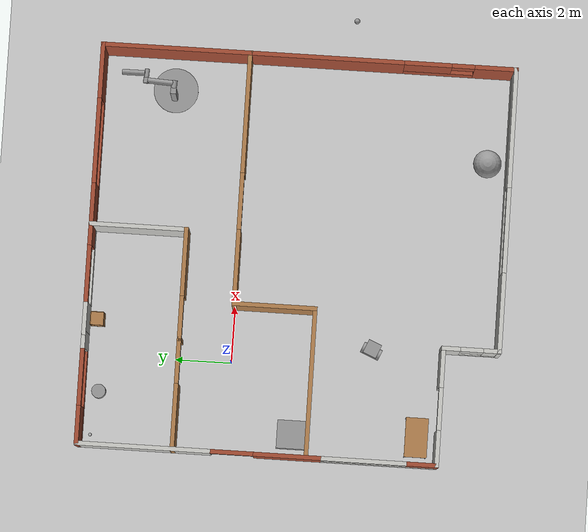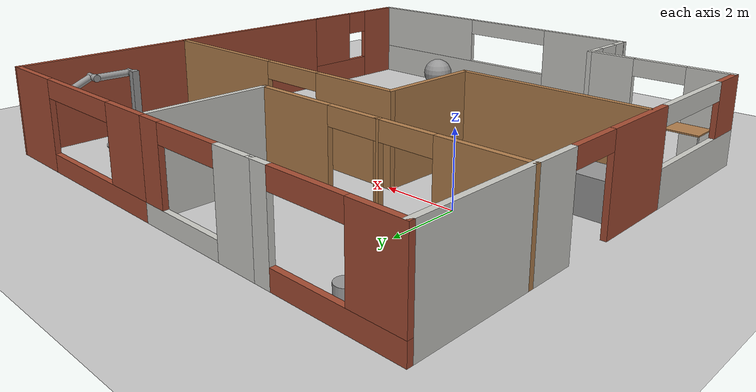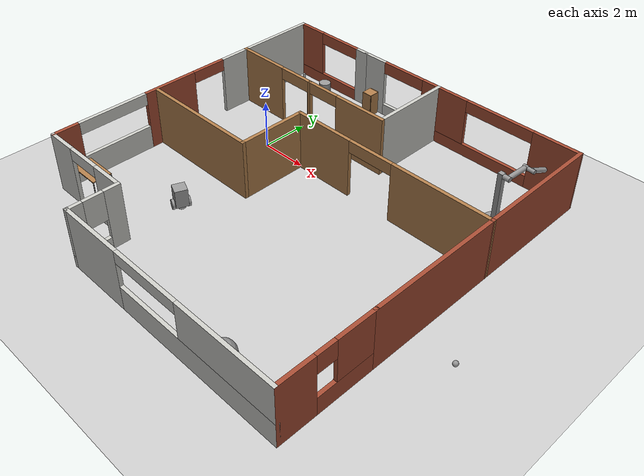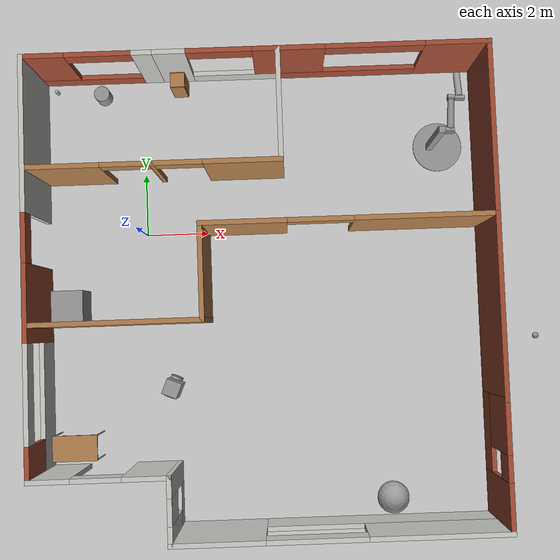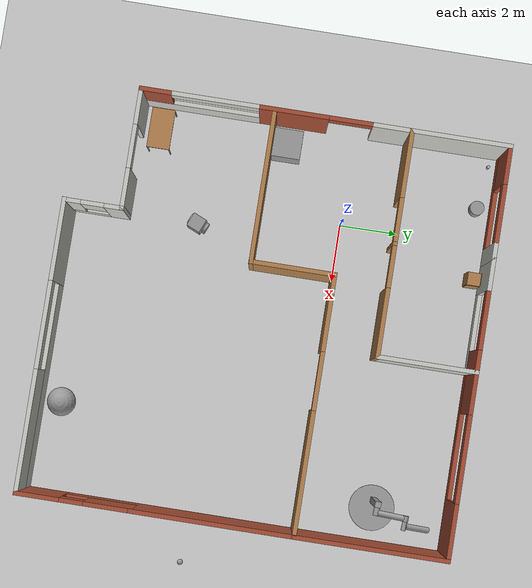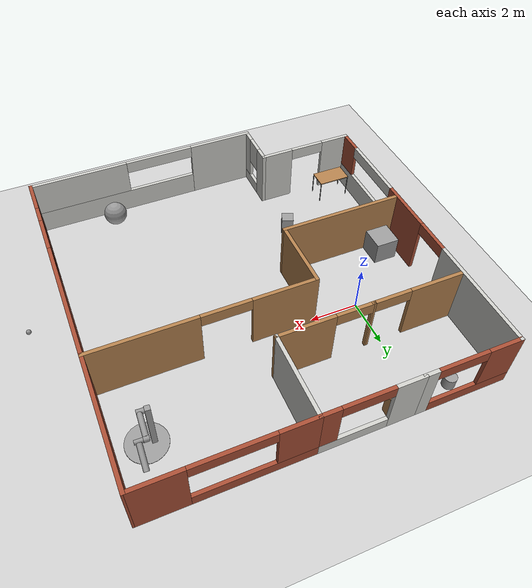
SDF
<sdf version="1.6">
 <world name="default">
  <plugin name="hello" filename="libhello.so"/>
  <light name="sun" type="directional">
   <pose>0 0 10 0 -0 0</pose>
   <diffuse>0.8 0.8 0.8 1</diffuse>
   <specular>0.1 0.1 0.1 1</specular>
   <attenuation>
    <range>1000</range>
    <constant>0.9</constant>
    <linear>0.01</linear>
    <quadratic>0.001</quadratic>
   </attenuation>
   <direction>-0.5 0.5 -1</direction>
  </light>
  <model name="ground_plane">
   <static>1</static>
   <link name="link">
    <collision name="collision">
     <geometry><plane><normal>0 0 1</normal><size>100 100</size></plane></geometry>
     <surface><friction><ode><mu>100</mu><mu2>50</mu2></ode></friction></surface>
    </collision>
    <visual name="visual">
     <cast_shadows>0</cast_shadows>
     <geometry><plane><normal>0 0 1</normal><size>100 100</size></plane></geometry>
     <material>
      <script><uri>file://media/materials/scripts/gazebo.material</uri><name>Gazebo/Grey</name></script>
     </material>
    </visual>
   </link>
  </model>
  <gravity>0 0 -9.8</gravity>
  <magnetic_field>6e-06 2.3e-05 -4.2e-05</magnetic_field>
  <atmosphere type="adiabatic"/>
  <physics name="default_physics" default="0" type="ode">
   <max_step_size>0.001</max_step_size>
   <real_time_factor>1</real_time_factor>
   <real_time_update_rate>1000</real_time_update_rate>
  </physics>
  <scene><ambient>0.4 0.4 0.4 1</ambient><background>0.7 0.7 0.7 1</background><shadows>1</shadows></scene>
  <spherical_coordinates>
   <surface_model>EARTH_WGS84</surface_model>
   <latitude_deg>0</latitude_deg>
   <longitude_deg>0</longitude_deg>
   <elevation>0</elevation>
   <heading_deg>0</heading_deg>
  </spherical_coordinates>
  <model name="myrobot">
   <link name="link_0">
    <pose>0.0125 0 0.28125 0 -0 0</pose>
    <inertial>
     <mass>1</mass>
     <inertia>
      <ixx>0.166667</ixx>
      <ixy>0</ixy>
      <ixz>0</ixz>
      <iyy>0.166667</iyy>
      <iyz>0</iyz>
      <izz>0.166667</izz>
     </inertia>
    </inertial>
    <visual name="visual">
     <geometry><box><size>0.5 0.5 0.75</size></box></geometry>
     <material>
      <lighting>1</lighting>
      <script><uri>file://media/materials/scripts/gazebo.material</uri><name>Gazebo/Grey</name></script>
      <ambient>0.3 0.3 0.3 1</ambient>
      <diffuse>0.7 0.7 0.7 1</diffuse>
      <specular>0.01 0.01 0.01 1</specular>
      <emissive>0 0 0 1</emissive>
      <shader type="vertex"><normal_map>__default__</normal_map></shader>
     </material>
    </visual>
    <collision name="collision">
     <geometry><box><size>0.5 0.5 0.75</size></box></geometry>
     <surface>
      <friction>
       <ode><mu>1</mu><mu2>1</mu2><fdir1>0 0 0</fdir1><slip1>0</slip1><slip2>0</slip2></ode>
       <torsional>
        <coefficient>1</coefficient>
        <patch_radius>0</patch_radius>
        <surface_radius>0</surface_radius>
        <use_patch_radius>1</use_patch_radius>
        <ode><slip>0</slip></ode>
       </torsional>
      </friction>
      <bounce><restitution_coefficient>0</restitution_coefficient><threshold>1e+06</threshold></bounce>
      <contact>
       <collide_without_contact>0</collide_without_contact>
       <collide_without_contact_bitmask>1</collide_without_contact_bitmask>
       <collide_bitmask>1</collide_bitmask>
       <ode>
        <soft_cfm>0</soft_cfm>
        <soft_erp>0.2</soft_erp>
        <kp>1e+13</kp>
        <kd>1</kd>
        <max_vel>0.01</max_vel>
        <min_depth>0</min_depth>
       </ode>
       <bullet>
        <split_impulse>1</split_impulse>
        <split_impulse_penetration_threshold>-0.01</split_impulse_penetration_threshold>
        <soft_cfm>0</soft_cfm>
        <soft_erp>0.2</soft_erp>
        <kp>1e+13</kp>
        <kd>1</kd>
       </bullet>
      </contact>
     </surface>
    </collision>
   </link>
   <link name="link_1">
    <pose>-0.0375 0.300019 -0.09375 1.5707 -0 0</pose>
    <inertial>
     <mass>1</mass>
     <inertia><ixx>0.145833</ixx><ixy>0</ixy><ixz>0</ixz><iyy>0.145833</iyy><iyz>0</iyz><izz>0.125</izz></inertia>
    </inertial>
    <visual name="visual">
     <geometry><cylinder><radius>0.2</radius><length>0.1</length></cylinder></geometry>
     <material>
      <lighting>1</lighting>
      <script><uri>file://media/materials/scripts/gazebo.material</uri><name>Gazebo/Grey</name></script>
      <ambient>0.3 0.3 0.3 1</ambient>
      <diffuse>0.7 0.7 0.7 1</diffuse>
      <specular>0.01 0.01 0.01 1</specular>
      <emissive>0 0 0 1</emissive>
      <shader type="vertex"><normal_map>__default__</normal_map></shader>
     </material>
    </visual>
    <collision name="collision">
     <geometry><cylinder><radius>0.2</radius><length>0.1</length></cylinder></geometry>
     <surface>
      <friction>
       <ode><mu>1</mu><mu2>1</mu2><fdir1>0 0 0</fdir1><slip1>0</slip1><slip2>0</slip2></ode>
       <torsional>
        <coefficient>1</coefficient>
        <patch_radius>0</patch_radius>
        <surface_radius>0</surface_radius>
        <use_patch_radius>1</use_patch_radius>
        <ode><slip>0</slip></ode>
       </torsional>
      </friction>
      <bounce><restitution_coefficient>0</restitution_coefficient><threshold>1e+06</threshold></bounce>
      <contact>
       <collide_without_contact>0</collide_without_contact>
       <collide_without_contact_bitmask>1</collide_without_contact_bitmask>
       <collide_bitmask>1</collide_bitmask>
       <ode>
        <soft_cfm>0</soft_cfm>
        <soft_erp>0.2</soft_erp>
        <kp>1e+13</kp>
        <kd>1</kd>
        <max_vel>0.01</max_vel>
        <min_depth>0</min_depth>
       </ode>
       <bullet>
        <split_impulse>1</split_impulse>
        <split_impulse_penetration_threshold>-0.01</split_impulse_penetration_threshold>
        <soft_cfm>0</soft_cfm>
        <soft_erp>0.2</soft_erp>
        <kp>1e+13</kp>
        <kd>1</kd>
       </bullet>
      </contact>
     </surface>
    </collision>
   </link>
   <link name="link_1_clone">
    <pose>-0.0375 -0.300019 -0.09375 1.5707 -0 0</pose>
    <inertial>
     <mass>1</mass>
     <inertia><ixx>0.145833</ixx><ixy>0</ixy><ixz>0</ixz><iyy>0.145833</iyy><iyz>0</iyz><izz>0.125</izz></inertia>
    </inertial>
    <visual name="visual">
     <geometry><cylinder><radius>0.2</radius><length>0.1</length></cylinder></geometry>
     <material>
      <lighting>1</lighting>
      <script><uri>file://media/materials/scripts/gazebo.material</uri><name>Gazebo/Grey</name></script>
      <ambient>0.3 0.3 0.3 1</ambient>
      <diffuse>0.7 0.7 0.7 1</diffuse>
      <specular>0.01 0.01 0.01 1</specular>
      <emissive>0 0 0 1</emissive>
      <shader type="vertex"><normal_map>__default__</normal_map></shader>
     </material>
    </visual>
    <collision name="collision">
     <geometry><cylinder><radius>0.2</radius><length>0.1</length></cylinder></geometry>
     <surface>
      <friction>
       <ode><mu>1</mu><mu2>1</mu2><fdir1>0 0 0</fdir1><slip1>0</slip1><slip2>0</slip2></ode>
       <torsional>
        <coefficient>1</coefficient>
        <patch_radius>0</patch_radius>
        <surface_radius>0</surface_radius>
        <use_patch_radius>1</use_patch_radius>
        <ode><slip>0</slip></ode>
       </torsional>
      </friction>
      <bounce><restitution_coefficient>0</restitution_coefficient><threshold>1e+06</threshold></bounce>
      <contact>
       <collide_without_contact>0</collide_without_contact>
       <collide_without_contact_bitmask>1</collide_without_contact_bitmask>
       <collide_bitmask>1</collide_bitmask>
       <ode>
        <soft_cfm>0</soft_cfm>
        <soft_erp>0.2</soft_erp>
        <kp>1e+13</kp>
        <kd>1</kd>
        <max_vel>0.01</max_vel>
        <min_depth>0</min_depth>
       </ode>
       <bullet>
        <split_impulse>1</split_impulse>
        <split_impulse_penetration_threshold>-0.01</split_impulse_penetration_threshold>
        <soft_cfm>0</soft_cfm>
        <soft_erp>0.2</soft_erp>
        <kp>1e+13</kp>
        <kd>1</kd>
       </bullet>
      </contact>
     </surface>
    </collision>
   </link>
   <link name="link_2">
    <pose>0.0625 0 -0.09375 0 -0 0</pose>
    <inertial>
     <mass>1</mass>
     <inertia><ixx>0.1</ixx><ixy>0</ixy><ixz>0</ixz><iyy>0.1</iyy><iyz>0</iyz><izz>0.1</izz></inertia>
    </inertial>
    <visual name="visual">
     <geometry><sphere><radius>0.2</radius></sphere></geometry>
     <material>
      <lighting>1</lighting>
      <script><uri>file://media/materials/scripts/gazebo.material</uri><name>Gazebo/Grey</name></script>
      <ambient>0.3 0.3 0.3 1</ambient>
      <diffuse>0.7 0.7 0.7 1</diffuse>
      <specular>0.01 0.01 0.01 1</specular>
      <emissive>0 0 0 1</emissive>
      <shader type="vertex"><normal_map>__default__</normal_map></shader>
     </material>
    </visual>
    <collision name="collision">
     <geometry><sphere><radius>0.2</radius></sphere></geometry>
     <surface>
      <friction>
       <ode><mu>1</mu><mu2>1</mu2><fdir1>0 0 0</fdir1><slip1>0</slip1><slip2>0</slip2></ode>
       <torsional>
        <coefficient>1</coefficient>
        <patch_radius>0</patch_radius>
        <surface_radius>0</surface_radius>
        <use_patch_radius>1</use_patch_radius>
        <ode><slip>0</slip></ode>
       </torsional>
      </friction>
      <bounce><restitution_coefficient>0</restitution_coefficient><threshold>1e+06</threshold></bounce>
      <contact>
       <collide_without_contact>0</collide_without_contact>
       <collide_without_contact_bitmask>1</collide_without_contact_bitmask>
       <collide_bitmask>1</collide_bitmask>
       <ode>
        <soft_cfm>0</soft_cfm>
        <soft_erp>0.2</soft_erp>
        <kp>1e+13</kp>
        <kd>1</kd>
        <max_vel>0.01</max_vel>
        <min_depth>0</min_depth>
       </ode>
       <bullet>
        <split_impulse>1</split_impulse>
        <split_impulse_penetration_threshold>-0.01</split_impulse_penetration_threshold>
        <soft_cfm>0</soft_cfm>
        <soft_erp>0.2</soft_erp>
        <kp>1e+13</kp>
        <kd>1</kd>
       </bullet>
      </contact>
     </surface>
    </collision>
   </link>
   <joint name="link_0_JOINT_1" type="revolute">
    <parent>link_0</parent>
    <child>link_1</child>
    <axis>
     <xyz>0 0 1</xyz>
     <use_parent_model_frame>0</use_parent_model_frame>
     <limit>
      <lower>-1.79769e+308</lower>
      <upper>1.79769e+308</upper>
      <effort>-1</effort>
      <velocity>-1</velocity>
     </limit>
     <dynamics>
      <spring_reference>0</spring_reference>
      <spring_stiffness>0</spring_stiffness>
      <damping>0</damping>
     </dynamics>
    </axis>
    <physics>
     <ode><limit><cfm>0</cfm><erp>0.2</erp></limit><suspension><cfm>0</cfm><erp>0.2</erp></suspension></ode>
    </physics>
   </joint>
   <joint name="link_0_JOINT_2" type="revolute">
    <parent>link_0</parent>
    <child>link_1_clone</child>
    <axis>
     <xyz>1 0 0</xyz>
     <use_parent_model_frame>0</use_parent_model_frame>
     <limit>
      <lower>-1.79769e+308</lower>
      <upper>1.79769e+308</upper>
      <effort>-1</effort>
      <velocity>-1</velocity>
     </limit>
     <dynamics>
      <spring_reference>0</spring_reference>
      <spring_stiffness>0</spring_stiffness>
      <damping>0</damping>
     </dynamics>
    </axis>
    <physics>
     <ode><limit><cfm>0</cfm><erp>0.2</erp></limit><suspension><cfm>0</cfm><erp>0.2</erp></suspension></ode>
    </physics>
   </joint>
   <joint name="link_0_JOINT_3" type="ball">
    <parent>link_0</parent>
    <child>link_2</child>
    <physics>
     <ode><limit><cfm>0</cfm><erp>0.2</erp></limit><suspension><cfm>0</cfm><erp>0.2</erp></suspension></ode>
    </physics>
   </joint>
   <static>0</static>
   <pose>0.769948 -4.95297 0.293751 7e-06 3.1e-05 -0.401224</pose>
  </model>
  <model name="my_ball">
   <link name="link_0">
    <inertial>
     <mass>1</mass>
     <inertia><ixx>0.1</ixx><ixy>0</ixy><ixz>0</ixz><iyy>0.1</iyy><iyz>0</iyz><izz>0.1</izz></inertia>
    </inertial>
    <visual name="visual">
     <geometry><sphere><radius>0.1</radius></sphere></geometry>
     <material>
      <lighting>1</lighting>
      <script><uri>file://media/materials/scripts/gazebo.material</uri><name>Gazebo/Grey</name></script>
      <ambient>1 1 1 1</ambient>
      <diffuse>1 1 1 1</diffuse>
      <specular>1 1 1 1</specular>
      <emissive>1 1 1 1</emissive>
      <shader type="vertex"><normal_map>__default__</normal_map></shader>
     </material>
    </visual>
    <collision name="collision">
     <geometry><sphere><radius>0.1</radius></sphere></geometry>
     <surface>
      <friction>
       <ode><mu>1</mu><mu2>1</mu2><fdir1>0 0 0</fdir1><slip1>0</slip1><slip2>0</slip2></ode>
       <torsional>
        <coefficient>1</coefficient>
        <patch_radius>0</patch_radius>
        <surface_radius>0</surface_radius>
        <use_patch_radius>1</use_patch_radius>
        <ode><slip>0</slip></ode>
       </torsional>
      </friction>
      <bounce><restitution_coefficient>0</restitution_coefficient><threshold>1e+06</threshold></bounce>
      <contact>
       <collide_without_contact>0</collide_without_contact>
       <collide_without_contact_bitmask>1</collide_without_contact_bitmask>
       <collide_bitmask>1</collide_bitmask>
       <ode>
        <soft_cfm>0</soft_cfm>
        <soft_erp>0.2</soft_erp>
        <kp>1e+13</kp>
        <kd>1</kd>
        <max_vel>0.01</max_vel>
        <min_depth>0</min_depth>
       </ode>
       <bullet>
        <split_impulse>1</split_impulse>
        <split_impulse_penetration_threshold>-0.01</split_impulse_penetration_threshold>
        <soft_cfm>0</soft_cfm>
        <soft_erp>0.2</soft_erp>
        <kp>1e+13</kp>
        <kd>1</kd>
       </bullet>
      </contact>
     </surface>
    </collision>
   </link>
   <static>0</static>
   <pose>12.5143 -3.70421 0.1 0 -0 0</pose>
  </model>
  <model name="double_pendulum_with_base">
   <link name="base">
    <inertial>
     <mass>100</mass>
     <inertia><ixx>1</ixx><ixy>0</ixy><ixz>0</ixz><iyy>1</iyy><iyz>0</iyz><izz>1</izz></inertia>
    </inertial>
    <visual name="vis_plate_on_ground">
     <pose>0 0 0.01 0 -0 0</pose>
     <geometry><cylinder><radius>0.8</radius><length>0.02</length></cylinder></geometry>
     <material>
      <script><uri>file://media/materials/scripts/gazebo.material</uri><name>Gazebo/Grey</name></script>
     </material>
    </visual>
    <visual name="vis_pole">
     <pose>-0.275 0 1.1 0 -0 0</pose>
     <geometry><box><size>0.2 0.2 2.2</size></box></geometry>
     <material>
      <script><uri>file://media/materials/scripts/gazebo.material</uri><name>Gazebo/Grey</name></script>
     </material>
    </visual>
    <collision name="col_plate_on_ground">
     <pose>0 0 0.01 0 -0 0</pose>
     <geometry><cylinder><radius>0.8</radius><length>0.02</length></cylinder></geometry>
    </collision>
    <collision name="col_pole">
     <pose>-0.275 0 1.1 0 -0 0</pose>
     <geometry><box><size>0.2 0.2 2.2</size></box></geometry>
    </collision>
   </link>
   <link name="upper_link">
    <pose>0 0 2.1 -1.5708 0 0</pose>
    <inertial>
     <pose>0 0 0.5 0 -0 0</pose>
     <inertia><ixx>1</ixx><ixy>0</ixy><ixz>0</ixz><iyy>1</iyy><iyz>0</iyz><izz>1</izz></inertia>
     <mass>1</mass>
    </inertial>
    <visual name="vis_upper_joint">
     <pose>-0.05 0 0 3.14159 1.57079 3.14159</pose>
     <geometry><cylinder><radius>0.1</radius><length>0.3</length></cylinder></geometry>
     <material>
      <script><uri>file://media/materials/scripts/gazebo.material</uri><name>Gazebo/Grey</name></script>
     </material>
    </visual>
    <visual name="vis_lower_joint">
     <pose>0 0 1 3.14159 1.57079 3.14159</pose>
     <geometry><cylinder><radius>0.1</radius><length>0.2</length></cylinder></geometry>
     <material>
      <script><uri>file://media/materials/scripts/gazebo.material</uri><name>Gazebo/Grey</name></script>
     </material>
    </visual>
    <visual name="vis_cylinder">
     <pose>0 0 0.5 0 -0 0</pose>
     <geometry><cylinder><radius>0.1</radius><length>0.9</length></cylinder></geometry>
     <material>
      <script><uri>file://media/materials/scripts/gazebo.material</uri><name>Gazebo/Grey</name></script>
     </material>
    </visual>
    <collision name="col_upper_joint">
     <pose>-0.05 0 0 3.14159 1.57079 3.14159</pose>
     <geometry><cylinder><radius>0.1</radius><length>0.3</length></cylinder></geometry>
    </collision>
    <collision name="col_lower_joint">
     <pose>0 0 1 3.14159 1.57079 3.14159</pose>
     <geometry><cylinder><radius>0.1</radius><length>0.2</length></cylinder></geometry>
    </collision>
    <collision name="col_cylinder">
     <pose>0 0 0.5 0 -0 0</pose>
     <geometry><cylinder><radius>0.1</radius><length>0.9</length></cylinder></geometry>
    </collision>
   </link>
   <link name="lower_link">
    <pose>0.25 1 2.1 -2 0 0</pose>
    <inertial>
     <pose>0 0 0.5 0 -0 0</pose>
     <inertia><ixx>1</ixx><ixy>0</ixy><ixz>0</ixz><iyy>1</iyy><iyz>0</iyz><izz>1</izz></inertia>
     <mass>1</mass>
    </inertial>
    <visual name="vis_lower_joint">
     <pose>0 0 0 3.14159 1.57079 3.14159</pose>
     <geometry><cylinder><radius>0.08</radius><length>0.3</length></cylinder></geometry>
     <material>
      <script><uri>file://media/materials/scripts/gazebo.material</uri><name>Gazebo/Grey</name></script>
     </material>
    </visual>
    <visual name="vis_cylinder">
     <pose>0 0 0.5 0 -0 0</pose>
     <geometry><cylinder><radius>0.1</radius><length>0.9</length></cylinder></geometry>
     <material>
      <script><uri>file://media/materials/scripts/gazebo.material</uri><name>Gazebo/Grey</name></script>
     </material>
    </visual>
    <collision name="col_lower_joint">
     <pose>0 0 0 3.14159 1.57079 3.14159</pose>
     <geometry><cylinder><radius>0.08</radius><length>0.3</length></cylinder></geometry>
    </collision>
    <collision name="col_cylinder">
     <pose>0 0 0.5 0 -0 0</pose>
     <geometry><cylinder><radius>0.1</radius><length>0.9</length></cylinder></geometry>
    </collision>
   </link>
   <joint name="upper_joint" type="revolute">
    <parent>base</parent>
    <child>upper_link</child>
    <axis>
     <xyz>1 0 0</xyz>
     <use_parent_model_frame>1</use_parent_model_frame>
     <limit><lower>-1e+16</lower><upper>1e+16</upper></limit>
     <dynamics><spring_reference>0</spring_reference><spring_stiffness>0</spring_stiffness></dynamics>
    </axis>
   </joint>
   <joint name="lower_joint" type="revolute">
    <parent>upper_link</parent>
    <child>lower_link</child>
    <axis>
     <xyz>1 0 0</xyz>
     <use_parent_model_frame>1</use_parent_model_frame>
     <limit><lower>-1e+16</lower><upper>1e+16</upper></limit>
     <dynamics><spring_reference>0</spring_reference><spring_stiffness>0</spring_stiffness></dynamics>
    </axis>
   </joint>
   <pose>9.61585 2.60855 0 0 0 -0.051707</pose>
  </model>
  <model name="unit_cylinder_0_0">
   <link name="link">
    <inertial>
     <mass>1</mass>
     <inertia><ixx>0.145833</ixx><ixy>0</ixy><ixz>0</ixz><iyy>0.145833</iyy><iyz>0</iyz><izz>0.125</izz></inertia>
    </inertial>
    <visual name="visual">
     <geometry><cylinder><radius>0.25</radius><length>0.5</length></cylinder></geometry>
     <material>
      <script><name>Gazebo/Grey</name><uri>file://media/materials/scripts/gazebo.material</uri></script>
      <ambient>0.3 0.3 0.3 1</ambient>
      <diffuse>0.7 0.7 0.7 1</diffuse>
      <specular>0.01 0.01 0.01 1</specular>
      <emissive>0 0 0 1</emissive>
      <shader type="vertex"><normal_map>__default__</normal_map></shader>
     </material>
    </visual>
    <collision name="collision">
     <geometry><cylinder><radius>0.25</radius><length>0.5</length></cylinder></geometry>
     <surface>
      <friction>
       <ode><mu>1</mu><mu2>1</mu2><fdir1>0 0 0</fdir1><slip1>0</slip1><slip2>0</slip2></ode>
       <torsional>
        <coefficient>1</coefficient>
        <patch_radius>0</patch_radius>
        <surface_radius>0</surface_radius>
        <use_patch_radius>1</use_patch_radius>
        <ode><slip>0</slip></ode>
       </torsional>
      </friction>
      <bounce><restitution_coefficient>0</restitution_coefficient><threshold>1e+06</threshold></bounce>
      <contact>
       <collide_without_contact>0</collide_without_contact>
       <collide_without_contact_bitmask>1</collide_without_contact_bitmask>
       <collide_bitmask>1</collide_bitmask>
       <ode>
        <soft_cfm>0</soft_cfm>
        <soft_erp>0.2</soft_erp>
        <kp>1e+13</kp>
        <kd>1</kd>
        <max_vel>0.01</max_vel>
        <min_depth>0</min_depth>
       </ode>
       <bullet>
        <split_impulse>1</split_impulse>
        <split_impulse_penetration_threshold>-0.01</split_impulse_penetration_threshold>
        <soft_cfm>0</soft_cfm>
        <soft_erp>0.2</soft_erp>
        <kp>1e+13</kp>
        <kd>1</kd>
       </bullet>
      </contact>
     </surface>
    </collision>
   </link>
   <static>0</static>
   <pose>-1.30437 4.62965 0.249991 0 -0 0</pose>
  </model>
  <model name="beer">
   <link name="link">
    <pose>0 0 0.115 0 -0 0</pose>
    <inertial>
     <mass>0.39</mass>
     <inertia><ixx>0.00058</ixx><ixy>0</ixy><ixz>0</ixz><iyy>0.00058</iyy><iyz>0</iyz><izz>0.00019</izz></inertia>
    </inertial>
    <collision name="collision">
     <geometry><cylinder><radius>0.055</radius><length>0.23</length></cylinder></geometry>
    </collision>
    <visual name="visual">
     <geometry><cylinder><radius>0.055</radius><length>0.23</length></cylinder></geometry>
     <material>
      <script>
       <uri>model://beer/materials/scripts</uri>
       <uri>model://beer/materials/textures</uri>
       <name>Beer/Diffuse</name>
      </script>
     </material>
    </visual>
   </link>
   <pose>-2.85151 4.84104 -7e-06 0 0 -3.3e-05</pose>
  </model>
  <model name="cabinet">
   <static>1</static>
   <link name="cabinet_bottom_plate">
    <inertial>
     <pose>0 0 -1 0 -0 0</pose>
     <inertia><ixx>2.05</ixx><ixy>0</ixy><ixz>0</ixz><iyy>2.05</iyy><iyz>0</iyz><izz>2.05</izz></inertia>
     <mass>25</mass>
    </inertial>
    <collision name="cabinet_bottom_plate_geom">
     <pose>0 0 0.01 0 -0 0</pose>
     <geometry><box><size>0.45 0.45 0.02</size></box></geometry>
    </collision>
    <visual name="cabinet_bottom_plate_geom_visual">
     <pose>0 0 0.01 0 -0 0</pose>
     <geometry><box><size>0.45 0.45 0.02</size></box></geometry>
     <material>
      <script><uri>file://media/materials/scripts/gazebo.material</uri><name>Gazebo/Wood</name></script>
     </material>
    </visual>
    <collision name="cabinet_bottom_plate_geom_cabinet_back_plate">
     <pose>0.235 0 0.51 0 -0 0</pose>
     <geometry><box><size>0.02 0.45 1.02</size></box></geometry>
    </collision>
    <visual name="cabinet_bottom_plate_geom_cabinet_back_plate_visual">
     <pose>0.235 0 0.51 0 -0 0</pose>
     <geometry><box><size>0.02 0.45 1.02</size></box></geometry>
     <material>
      <script><uri>file://media/materials/scripts/gazebo.material</uri><name>Gazebo/Wood</name></script>
     </material>
    </visual>
    <collision name="cabinet_bottom_plate_geom_cabinet_left_plate">
     <pose>0 0.235 0.51 0 -0 0</pose>
     <geometry><box><size>0.45 0.02 1.02</size></box></geometry>
    </collision>
    <visual name="cabinet_bottom_plate_geom_cabinet_left_plate_visual">
     <pose>0 0.235 0.51 0 -0 0</pose>
     <geometry><box><size>0.45 0.02 1.02</size></box></geometry>
     <material>
      <script><uri>file://media/materials/scripts/gazebo.material</uri><name>Gazebo/Wood</name></script>
     </material>
    </visual>
    <collision name="cabinet_bottom_plate_geom_cabinet_middle_plate">
     <pose>0 0 0.51 0 -0 0</pose>
     <geometry><box><size>0.45 0.45 0.02</size></box></geometry>
    </collision>
    <visual name="cabinet_bottom_plate_geom_cabinet_middle_plate_visual">
     <pose>0 0 0.51 0 -0 0</pose>
     <geometry><box><size>0.45 0.45 0.02</size></box></geometry>
     <material>
      <script><uri>file://media/materials/scripts/gazebo.material</uri><name>Gazebo/Wood</name></script>
     </material>
    </visual>
    <collision name="cabinet_bottom_plate_geom_cabinet_right_plate">
     <pose>0 -0.235 0.51 0 -0 0</pose>
     <geometry><box><size>0.45 0.02 1.02</size></box></geometry>
    </collision>
    <visual name="cabinet_bottom_plate_geom_cabinet_right_plate_visual">
     <pose>0 -0.235 0.51 0 -0 0</pose>
     <geometry><box><size>0.45 0.02 1.02</size></box></geometry>
     <material>
      <script><uri>file://media/materials/scripts/gazebo.material</uri><name>Gazebo/Wood</name></script>
     </material>
    </visual>
    <collision name="cabinet_bottom_plate_geom_cabinet_top_plate">
     <pose>0 0 1.01 0 -0 0</pose>
     <geometry><box><size>0.45 0.45 0.02</size></box></geometry>
    </collision>
    <visual name="cabinet_bottom_plate_geom_cabinet_top_plate_visual">
     <pose>0 0 1.01 0 -0 0</pose>
     <geometry><box><size>0.45 0.45 0.02</size></box></geometry>
     <material>
      <script><uri>file://media/materials/scripts/gazebo.material</uri><name>Gazebo/Wood</name></script>
     </material>
    </visual>
   </link>
   <pose>1.23212 4.82503 0 0 -0 0</pose>
  </model>
  <model name="table">
   <static>0</static>
   <link name="link">
    <collision name="surface">
     <pose>0 0 1 0 -0 0</pose>
     <geometry><box><size>1.5 0.8 0.03</size></box></geometry>
     <surface><friction><ode><mu>0.6</mu><mu2>0.6</mu2></ode></friction></surface>
    </collision>
    <visual name="visual1">
     <pose>0 0 1 0 -0 0</pose>
     <geometry><box><size>1.4 0.8 0.04</size></box></geometry>
     <material>
      <script><uri>file://media/materials/scripts/gazebo.material</uri><name>Gazebo/Wood</name></script>
     </material>
    </visual>
    <collision name="front_left_leg">
     <pose>0.68 0.38 0.5 0 -0 0</pose>
     <geometry><cylinder><radius>0.02</radius><length>1</length></cylinder></geometry>
    </collision>
    <visual name="front_left_leg">
     <pose>0.68 0.38 0.5 0 -0 0</pose>
     <geometry><cylinder><radius>0.02</radius><length>1</length></cylinder></geometry>
     <material>
      <script><uri>file://media/materials/scripts/gazebo.material</uri><name>Gazebo/Grey</name></script>
     </material>
    </visual>
    <collision name="front_right_leg">
     <pose>0.68 -0.38 0.5 0 -0 0</pose>
     <geometry><cylinder><radius>0.02</radius><length>1</length></cylinder></geometry>
    </collision>
    <visual name="front_right_leg">
     <pose>0.68 -0.38 0.5 0 -0 0</pose>
     <geometry><cylinder><radius>0.02</radius><length>1</length></cylinder></geometry>
     <material>
      <script><uri>file://media/materials/scripts/gazebo.material</uri><name>Gazebo/Grey</name></script>
     </material>
    </visual>
    <collision name="back_right_leg">
     <pose>-0.68 -0.38 0.5 0 -0 0</pose>
     <geometry><cylinder><radius>0.02</radius><length>1</length></cylinder></geometry>
    </collision>
    <visual name="back_right_leg">
     <pose>-0.68 -0.38 0.5 0 -0 0</pose>
     <geometry><cylinder><radius>0.02</radius><length>1</length></cylinder></geometry>
     <material>
      <script><uri>file://media/materials/scripts/gazebo.material</uri><name>Gazebo/Grey</name></script>
     </material>
    </visual>
    <collision name="back_left_leg">
     <pose>-0.68 0.38 0.5 0 -0 0</pose>
     <geometry><cylinder><radius>0.02</radius><length>1</length></cylinder></geometry>
    </collision>
    <visual name="back_left_leg">
     <pose>-0.68 0.38 0.5 0 -0 0</pose>
     <geometry><cylinder><radius>0.02</radius><length>1</length></cylinder></geometry>
     <material>
      <script><uri>file://media/materials/scripts/gazebo.material</uri><name>Gazebo/Grey</name></script>
     </material>
    </visual>
    <inertial>
     <inertia><ixx>1</ixx><ixy>0</ixy><ixz>0</ixz><iyy>1</iyy><iyz>0</iyz><izz>1</izz></inertia>
     <mass>1</mass>
    </inertial>
   </link>
   <pose>-2.25774 -6.69519 -1e-06 0 1e-06 0</pose>
  </model>
  <model name="mybuilding_0_0_0_0">
   <link name="Wall_100">
    <pose>-4.97405 -5.32475 0 0 -0 0</pose>
    <inertial>
     <mass>1</mass>
     <inertia><ixx>1</ixx><ixy>0</ixy><ixz>0</ixz><iyy>1</iyy><iyz>0</iyz><izz>1</izz></inertia>
    </inertial>
    <visual name="Wall_100_Visual_0">
     <pose>-1.47284 0 1.25 0 -0 0</pose>
     <geometry><box><size>1.30431 0.15 2.5</size></box></geometry>
     <material>
      <script><uri>file://media/materials/scripts/gazebo.material</uri><name>Gazebo/CeilingTiled</name></script>
      <ambient>0.435 0.796 0.675 1</ambient>
      <diffuse>1 1 1 1</diffuse>
      <specular>0 0 0 1</specular>
      <emissive>0 0 0 1</emissive>
      <shader type="vertex"><normal_map>__default__</normal_map></shader>
     </material>
    </visual>
    <visual name="Wall_100_Visual_1">
     <pose>1.40216 0 1.25 0 -0 0</pose>
     <geometry><box><size>1.44569 0.15 2.5</size></box></geometry>
     <material>
      <script><uri>file://media/materials/scripts/gazebo.material</uri><name>Gazebo/CeilingTiled</name></script>
      <ambient>0.435 0.796 0.675 1</ambient>
      <diffuse>1 1 1 1</diffuse>
      <specular>0 0 0 1</specular>
      <emissive>0 0 0 1</emissive>
      <shader type="vertex"><normal_map>__default__</normal_map></shader>
     </material>
    </visual>
    <visual name="Wall_100_Visual_2">
     <pose>-0.07069 0 2.25 0 -0 0</pose>
     <geometry><box><size>1.5 0.15 0.5</size></box></geometry>
     <material>
      <script><uri>file://media/materials/scripts/gazebo.material</uri><name>Gazebo/CeilingTiled</name></script>
      <ambient>0.435 0.796 0.675 1</ambient>
      <diffuse>1 1 1 1</diffuse>
      <specular>0 0 0 1</specular>
      <emissive>0 0 0 1</emissive>
      <shader type="vertex"><normal_map>__default__</normal_map></shader>
     </material>
    </visual>
    <collision name="Wall_100_Collision_0">
     <pose>-1.47284 0 1.25 0 -0 0</pose>
     <geometry><box><size>1.30431 0.15 2.5</size></box></geometry>
     <surface>
      <friction>
       <ode><mu>1</mu><mu2>1</mu2><fdir1>0 0 0</fdir1><slip1>0</slip1><slip2>0</slip2></ode>
       <torsional>
        <coefficient>1</coefficient>
        <patch_radius>0</patch_radius>
        <surface_radius>0</surface_radius>
        <use_patch_radius>1</use_patch_radius>
        <ode><slip>0</slip></ode>
       </torsional>
      </friction>
      <bounce><restitution_coefficient>0</restitution_coefficient><threshold>1e+06</threshold></bounce>
      <contact>
       <collide_without_contact>0</collide_without_contact>
       <collide_without_contact_bitmask>1</collide_without_contact_bitmask>
       <collide_bitmask>1</collide_bitmask>
       <ode>
        <soft_cfm>0</soft_cfm>
        <soft_erp>0.2</soft_erp>
        <kp>1e+13</kp>
        <kd>1</kd>
        <max_vel>0.01</max_vel>
        <min_depth>0</min_depth>
       </ode>
       <bullet>
        <split_impulse>1</split_impulse>
        <split_impulse_penetration_threshold>-0.01</split_impulse_penetration_threshold>
        <soft_cfm>0</soft_cfm>
        <soft_erp>0.2</soft_erp>
        <kp>1e+13</kp>
        <kd>1</kd>
       </bullet>
      </contact>
     </surface>
    </collision>
    <collision name="Wall_100_Collision_1">
     <pose>1.40216 0 1.25 0 -0 0</pose>
     <geometry><box><size>1.44569 0.15 2.5</size></box></geometry>
     <surface>
      <friction>
       <ode><mu>1</mu><mu2>1</mu2><fdir1>0 0 0</fdir1><slip1>0</slip1><slip2>0</slip2></ode>
       <torsional>
        <coefficient>1</coefficient>
        <patch_radius>0</patch_radius>
        <surface_radius>0</surface_radius>
        <use_patch_radius>1</use_patch_radius>
        <ode><slip>0</slip></ode>
       </torsional>
      </friction>
      <bounce><restitution_coefficient>0</restitution_coefficient><threshold>1e+06</threshold></bounce>
      <contact>
       <collide_without_contact>0</collide_without_contact>
       <collide_without_contact_bitmask>1</collide_without_contact_bitmask>
       <collide_bitmask>1</collide_bitmask>
       <ode>
        <soft_cfm>0</soft_cfm>
        <soft_erp>0.2</soft_erp>
        <kp>1e+13</kp>
        <kd>1</kd>
        <max_vel>0.01</max_vel>
        <min_depth>0</min_depth>
       </ode>
       <bullet>
        <split_impulse>1</split_impulse>
        <split_impulse_penetration_threshold>-0.01</split_impulse_penetration_threshold>
        <soft_cfm>0</soft_cfm>
        <soft_erp>0.2</soft_erp>
        <kp>1e+13</kp>
        <kd>1</kd>
       </bullet>
      </contact>
     </surface>
    </collision>
    <collision name="Wall_100_Collision_2">
     <pose>-0.07069 0 2.25 0 -0 0</pose>
     <geometry><box><size>1.5 0.15 0.5</size></box></geometry>
     <surface>
      <friction>
       <ode><mu>1</mu><mu2>1</mu2><fdir1>0 0 0</fdir1><slip1>0</slip1><slip2>0</slip2></ode>
       <torsional>
        <coefficient>1</coefficient>
        <patch_radius>0</patch_radius>
        <surface_radius>0</surface_radius>
        <use_patch_radius>1</use_patch_radius>
        <ode><slip>0</slip></ode>
       </torsional>
      </friction>
      <bounce><restitution_coefficient>0</restitution_coefficient><threshold>1e+06</threshold></bounce>
      <contact>
       <collide_without_contact>0</collide_without_contact>
       <collide_without_contact_bitmask>1</collide_without_contact_bitmask>
       <collide_bitmask>1</collide_bitmask>
       <ode>
        <soft_cfm>0</soft_cfm>
        <soft_erp>0.2</soft_erp>
        <kp>1e+13</kp>
        <kd>1</kd>
        <max_vel>0.01</max_vel>
        <min_depth>0</min_depth>
       </ode>
       <bullet>
        <split_impulse>1</split_impulse>
        <split_impulse_penetration_threshold>-0.01</split_impulse_penetration_threshold>
        <soft_cfm>0</soft_cfm>
        <soft_erp>0.2</soft_erp>
        <kp>1e+13</kp>
        <kd>1</kd>
       </bullet>
      </contact>
     </surface>
    </collision>
   </link>
   <link name="Wall_102">
    <pose>-2.91535 -6.30192 0 0 0 -1.5708</pose>
    <inertial>
     <mass>1</mass>
     <inertia><ixx>1</ixx><ixy>0</ixy><ixz>0</ixz><iyy>1</iyy><iyz>0</iyz><izz>1</izz></inertia>
    </inertial>
    <visual name="Wall_102_Visual_0">
     <pose>-0.715877 0 1.25 0 -0 0</pose>
     <geometry><box><size>0.672904 0.15 2.5</size></box></geometry>
     <material>
      <script><uri>file://media/materials/scripts/gazebo.material</uri><name>Gazebo/CeilingTiled</name></script>
      <ambient>1 0.765 0.306 1</ambient>
      <diffuse>1 1 1 1</diffuse>
      <specular>0 0 0 1</specular>
      <emissive>0 0 0 1</emissive>
      <shader type="vertex"><normal_map>__default__</normal_map></shader>
     </material>
    </visual>
    <visual name="Wall_102_Visual_1">
     <pose>0.336452 0 0.25 0 -0 0</pose>
     <geometry><box><size>1.43175 0.15 0.5</size></box></geometry>
     <material>
      <script><uri>file://media/materials/scripts/gazebo.material</uri><name>Gazebo/CeilingTiled</name></script>
      <ambient>1 0.765 0.306 1</ambient>
      <diffuse>1 1 1 1</diffuse>
      <specular>0 0 0 1</specular>
      <emissive>0 0 0 1</emissive>
      <shader type="vertex"><normal_map>__default__</normal_map></shader>
     </material>
    </visual>
    <visual name="Wall_102_Visual_3">
     <pose>0.020576 0 1.9 0 -0 0</pose>
     <geometry><box><size>0.8 0.15 1.2</size></box></geometry>
     <material>
      <script><uri>file://media/materials/scripts/gazebo.material</uri><name>Gazebo/CeilingTiled</name></script>
      <ambient>1 0.765 0.306 1</ambient>
      <diffuse>1 1 1 1</diffuse>
      <specular>0 0 0 1</specular>
      <emissive>0 0 0 1</emissive>
      <shader type="vertex"><normal_map>__default__</normal_map></shader>
     </material>
    </visual>
    <visual name="Wall_102_Visual_2">
     <pose>0.736452 0 1.5 0 -0 0</pose>
     <geometry><box><size>0.631753 0.15 2</size></box></geometry>
     <material>
      <script><uri>file://media/materials/scripts/gazebo.material</uri><name>Gazebo/CeilingTiled</name></script>
      <ambient>1 0.765 0.306 1</ambient>
      <diffuse>1 1 1 1</diffuse>
      <specular>0 0 0 1</specular>
      <emissive>0 0 0 1</emissive>
      <shader type="vertex"><normal_map>__default__</normal_map></shader>
     </material>
    </visual>
    <collision name="Wall_102_Collision_0">
     <pose>-0.715877 0 1.25 0 -0 0</pose>
     <geometry><box><size>0.672904 0.15 2.5</size></box></geometry>
     <surface>
      <friction>
       <ode><mu>1</mu><mu2>1</mu2><fdir1>0 0 0</fdir1><slip1>0</slip1><slip2>0</slip2></ode>
       <torsional>
        <coefficient>1</coefficient>
        <patch_radius>0</patch_radius>
        <surface_radius>0</surface_radius>
        <use_patch_radius>1</use_patch_radius>
        <ode><slip>0</slip></ode>
       </torsional>
      </friction>
      <bounce><restitution_coefficient>0</restitution_coefficient><threshold>1e+06</threshold></bounce>
      <contact>
       <collide_without_contact>0</collide_without_contact>
       <collide_without_contact_bitmask>1</collide_without_contact_bitmask>
       <collide_bitmask>1</collide_bitmask>
       <ode>
        <soft_cfm>0</soft_cfm>
        <soft_erp>0.2</soft_erp>
        <kp>1e+13</kp>
        <kd>1</kd>
        <max_vel>0.01</max_vel>
        <min_depth>0</min_depth>
       </ode>
       <bullet>
        <split_impulse>1</split_impulse>
        <split_impulse_penetration_threshold>-0.01</split_impulse_penetration_threshold>
        <soft_cfm>0</soft_cfm>
        <soft_erp>0.2</soft_erp>
        <kp>1e+13</kp>
        <kd>1</kd>
       </bullet>
      </contact>
     </surface>
    </collision>
    <collision name="Wall_102_Collision_3">
     <pose>0.020576 0 1.9 0 -0 0</pose>
     <geometry><box><size>0.8 0.15 1.2</size></box></geometry>
     <surface>
      <friction>
       <ode><mu>1</mu><mu2>1</mu2><fdir1>0 0 0</fdir1><slip1>0</slip1><slip2>0</slip2></ode>
       <torsional>
        <coefficient>1</coefficient>
        <patch_radius>0</patch_radius>
        <surface_radius>0</surface_radius>
        <use_patch_radius>1</use_patch_radius>
        <ode><slip>0</slip></ode>
       </torsional>
      </friction>
      <bounce><restitution_coefficient>0</restitution_coefficient><threshold>1e+06</threshold></bounce>
      <contact>
       <collide_without_contact>0</collide_without_contact>
       <collide_without_contact_bitmask>1</collide_without_contact_bitmask>
       <collide_bitmask>1</collide_bitmask>
       <ode>
        <soft_cfm>0</soft_cfm>
        <soft_erp>0.2</soft_erp>
        <kp>1e+13</kp>
        <kd>1</kd>
        <max_vel>0.01</max_vel>
        <min_depth>0</min_depth>
       </ode>
       <bullet>
        <split_impulse>1</split_impulse>
        <split_impulse_penetration_threshold>-0.01</split_impulse_penetration_threshold>
        <soft_cfm>0</soft_cfm>
        <soft_erp>0.2</soft_erp>
        <kp>1e+13</kp>
        <kd>1</kd>
       </bullet>
      </contact>
     </surface>
    </collision>
    <collision name="Wall_102_Collision_1">
     <pose>0.336452 0 0.25 0 -0 0</pose>
     <geometry><box><size>1.43175 0.15 0.5</size></box></geometry>
     <surface>
      <friction>
       <ode><mu>1</mu><mu2>1</mu2><fdir1>0 0 0</fdir1><slip1>0</slip1><slip2>0</slip2></ode>
       <torsional>
        <coefficient>1</coefficient>
        <patch_radius>0</patch_radius>
        <surface_radius>0</surface_radius>
        <use_patch_radius>1</use_patch_radius>
        <ode><slip>0</slip></ode>
       </torsional>
      </friction>
      <bounce><restitution_coefficient>0</restitution_coefficient><threshold>1e+06</threshold></bounce>
      <contact>
       <collide_without_contact>0</collide_without_contact>
       <collide_without_contact_bitmask>1</collide_without_contact_bitmask>
       <collide_bitmask>1</collide_bitmask>
       <ode>
        <soft_cfm>0</soft_cfm>
        <soft_erp>0.2</soft_erp>
        <kp>1e+13</kp>
        <kd>1</kd>
        <max_vel>0.01</max_vel>
        <min_depth>0</min_depth>
       </ode>
       <bullet>
        <split_impulse>1</split_impulse>
        <split_impulse_penetration_threshold>-0.01</split_impulse_penetration_threshold>
        <soft_cfm>0</soft_cfm>
        <soft_erp>0.2</soft_erp>
        <kp>1e+13</kp>
        <kd>1</kd>
       </bullet>
      </contact>
     </surface>
    </collision>
    <collision name="Wall_102_Collision_2">
     <pose>0.736452 0 1.5 0 -0 0</pose>
     <geometry><box><size>0.631753 0.15 2</size></box></geometry>
     <surface>
      <friction>
       <ode><mu>1</mu><mu2>1</mu2><fdir1>0 0 0</fdir1><slip1>0</slip1><slip2>0</slip2></ode>
       <torsional>
        <coefficient>1</coefficient>
        <patch_radius>0</patch_radius>
        <surface_radius>0</surface_radius>
        <use_patch_radius>1</use_patch_radius>
        <ode><slip>0</slip></ode>
       </torsional>
      </friction>
      <bounce><restitution_coefficient>0</restitution_coefficient><threshold>1e+06</threshold></bounce>
      <contact>
       <collide_without_contact>0</collide_without_contact>
       <collide_without_contact_bitmask>1</collide_without_contact_bitmask>
       <collide_bitmask>1</collide_bitmask>
       <ode>
        <soft_cfm>0</soft_cfm>
        <soft_erp>0.2</soft_erp>
        <kp>1e+13</kp>
        <kd>1</kd>
        <max_vel>0.01</max_vel>
        <min_depth>0</min_depth>
       </ode>
       <bullet>
        <split_impulse>1</split_impulse>
        <split_impulse_penetration_threshold>-0.01</split_impulse_penetration_threshold>
        <soft_cfm>0</soft_cfm>
        <soft_erp>0.2</soft_erp>
        <kp>1e+13</kp>
        <kd>1</kd>
       </bullet>
      </contact>
     </surface>
    </collision>
   </link>
   <link name="Wall_104">
    <pose>2.05282 -7.27925 0 0 0 -3.1e-05</pose>
    <visual name="Wall_104_Visual_0">
     <pose>-3.62649 0 1.25 0 -0 0</pose>
     <geometry><box><size>2.85075 0.15 2.5</size></box></geometry>
     <material>
      <script><uri>file://media/materials/scripts/gazebo.material</uri><name>Gazebo/CeilingTiled</name></script>
      <ambient>0.435294 0.796078 0.67451 1</ambient>
      <diffuse>1 1 1 1</diffuse>
      <specular>0 0 0 1</specular>
      <emissive>0 0 0 1</emissive>
     </material>
    </visual>
    <visual name="Wall_104_Visual_2">
     <pose>2.92537 0 1.75 0 -0 0</pose>
     <geometry><box><size>4.25299 0.15 1.5</size></box></geometry>
     <material>
      <script><uri>file://media/materials/scripts/gazebo.material</uri><name>Gazebo/CeilingTiled</name></script>
      <ambient>0.435294 0.796078 0.67451 1</ambient>
      <diffuse>1 1 1 1</diffuse>
      <specular>0 0 0 1</specular>
      <emissive>0 0 0 1</emissive>
     </material>
    </visual>
    <visual name="Wall_104_Visual_1">
     <pose>1.42538 0 0.5 0 -0 0</pose>
     <geometry><box><size>7.25299 0.15 1</size></box></geometry>
     <material>
      <script><uri>file://media/materials/scripts/gazebo.material</uri><name>Gazebo/CeilingTiled</name></script>
      <ambient>0.435294 0.796078 0.67451 1</ambient>
      <diffuse>1 1 1 1</diffuse>
      <specular>0 0 0 1</specular>
      <emissive>0 0 0 1</emissive>
     </material>
    </visual>
    <visual name="Wall_104_Visual_3">
     <pose>-0.70112 0 2.25 0 -0 0</pose>
     <geometry><box><size>3 0.15 0.5</size></box></geometry>
     <material>
      <script><uri>file://media/materials/scripts/gazebo.material</uri><name>Gazebo/CeilingTiled</name></script>
      <ambient>0.435294 0.796078 0.67451 1</ambient>
      <diffuse>1 1 1 1</diffuse>
      <specular>0 0 0 1</specular>
      <emissive>0 0 0 1</emissive>
     </material>
    </visual>
    <collision name="Wall_104_Collision_0">
     <pose>-3.62649 0 1.25 0 -0 0</pose>
     <geometry><box><size>2.85075 0.15 2.5</size></box></geometry>
     <surface>
      <friction>
       <ode><mu>1</mu><mu2>1</mu2><fdir1>0 0 0</fdir1><slip1>0</slip1><slip2>0</slip2></ode>
       <torsional>
        <coefficient>1</coefficient>
        <patch_radius>0</patch_radius>
        <surface_radius>0</surface_radius>
        <use_patch_radius>1</use_patch_radius>
        <ode><slip>0</slip></ode>
       </torsional>
      </friction>
      <bounce><restitution_coefficient>0</restitution_coefficient><threshold>1e+06</threshold></bounce>
      <contact>
       <collide_without_contact>0</collide_without_contact>
       <collide_without_contact_bitmask>1</collide_without_contact_bitmask>
       <collide_bitmask>1</collide_bitmask>
       <ode>
        <soft_cfm>0</soft_cfm>
        <soft_erp>0.2</soft_erp>
        <kp>1e+13</kp>
        <kd>1</kd>
        <max_vel>0.01</max_vel>
        <min_depth>0</min_depth>
       </ode>
       <bullet>
        <split_impulse>1</split_impulse>
        <split_impulse_penetration_threshold>-0.01</split_impulse_penetration_threshold>
        <soft_cfm>0</soft_cfm>
        <soft_erp>0.2</soft_erp>
        <kp>1e+13</kp>
        <kd>1</kd>
       </bullet>
      </contact>
     </surface>
    </collision>
    <collision name="Wall_104_Collision_2">
     <pose>2.92537 0 1.75 0 -0 0</pose>
     <geometry><box><size>4.25299 0.15 1.5</size></box></geometry>
     <surface>
      <friction>
       <ode><mu>1</mu><mu2>1</mu2><fdir1>0 0 0</fdir1><slip1>0</slip1><slip2>0</slip2></ode>
       <torsional>
        <coefficient>1</coefficient>
        <patch_radius>0</patch_radius>
        <surface_radius>0</surface_radius>
        <use_patch_radius>1</use_patch_radius>
        <ode><slip>0</slip></ode>
       </torsional>
      </friction>
      <bounce><restitution_coefficient>0</restitution_coefficient><threshold>1e+06</threshold></bounce>
      <contact>
       <collide_without_contact>0</collide_without_contact>
       <collide_without_contact_bitmask>1</collide_without_contact_bitmask>
       <collide_bitmask>1</collide_bitmask>
       <ode>
        <soft_cfm>0</soft_cfm>
        <soft_erp>0.2</soft_erp>
        <kp>1e+13</kp>
        <kd>1</kd>
        <max_vel>0.01</max_vel>
        <min_depth>0</min_depth>
       </ode>
       <bullet>
        <split_impulse>1</split_impulse>
        <split_impulse_penetration_threshold>-0.01</split_impulse_penetration_threshold>
        <soft_cfm>0</soft_cfm>
        <soft_erp>0.2</soft_erp>
        <kp>1e+13</kp>
        <kd>1</kd>
       </bullet>
      </contact>
     </surface>
    </collision>
    <collision name="Wall_104_Collision_1">
     <pose>1.42538 0 0.5 0 -0 0</pose>
     <geometry><box><size>7.25299 0.15 1</size></box></geometry>
     <surface>
      <friction>
       <ode><mu>1</mu><mu2>1</mu2><fdir1>0 0 0</fdir1><slip1>0</slip1><slip2>0</slip2></ode>
       <torsional>
        <coefficient>1</coefficient>
        <patch_radius>0</patch_radius>
        <surface_radius>0</surface_radius>
        <use_patch_radius>1</use_patch_radius>
        <ode><slip>0</slip></ode>
       </torsional>
      </friction>
      <bounce><restitution_coefficient>0</restitution_coefficient><threshold>1e+06</threshold></bounce>
      <contact>
       <collide_without_contact>0</collide_without_contact>
       <collide_without_contact_bitmask>1</collide_without_contact_bitmask>
       <collide_bitmask>1</collide_bitmask>
       <ode>
        <soft_cfm>0</soft_cfm>
        <soft_erp>0.2</soft_erp>
        <kp>1e+13</kp>
        <kd>1</kd>
        <max_vel>0.01</max_vel>
        <min_depth>0</min_depth>
       </ode>
       <bullet>
        <split_impulse>1</split_impulse>
        <split_impulse_penetration_threshold>-0.01</split_impulse_penetration_threshold>
        <soft_cfm>0</soft_cfm>
        <soft_erp>0.2</soft_erp>
        <kp>1e+13</kp>
        <kd>1</kd>
       </bullet>
      </contact>
     </surface>
    </collision>
    <collision name="Wall_104_Collision_3">
     <pose>-0.70112 0 2.25 0 -0 0</pose>
     <geometry><box><size>3 0.15 0.5</size></box></geometry>
     <surface>
      <friction>
       <ode><mu>1</mu><mu2>1</mu2><fdir1>0 0 0</fdir1><slip1>0</slip1><slip2>0</slip2></ode>
       <torsional>
        <coefficient>1</coefficient>
        <patch_radius>0</patch_radius>
        <surface_radius>0</surface_radius>
        <use_patch_radius>1</use_patch_radius>
        <ode><slip>0</slip></ode>
       </torsional>
      </friction>
      <bounce><restitution_coefficient>0</restitution_coefficient><threshold>1e+06</threshold></bounce>
      <contact>
       <collide_without_contact>0</collide_without_contact>
       <collide_without_contact_bitmask>1</collide_without_contact_bitmask>
       <collide_bitmask>1</collide_bitmask>
       <ode>
        <soft_cfm>0</soft_cfm>
        <soft_erp>0.2</soft_erp>
        <kp>1e+13</kp>
        <kd>1</kd>
        <max_vel>0.01</max_vel>
        <min_depth>0</min_depth>
       </ode>
       <bullet>
        <split_impulse>1</split_impulse>
        <split_impulse_penetration_threshold>-0.01</split_impulse_penetration_threshold>
        <soft_cfm>0</soft_cfm>
        <soft_erp>0.2</soft_erp>
        <kp>1e+13</kp>
        <kd>1</kd>
       </bullet>
      </contact>
     </surface>
    </collision>
   </link>
   <link name="Wall_106">
    <pose>7.02969 -5.3499 0 0 -0 1.5708</pose>
    <visual name="Wall_106_Visual_2">
     <pose>1.16691 0 1.625 0 -0 0</pose>
     <geometry><box><size>1.67484 0.15 1.75</size></box></geometry>
     <material>
      <script><uri>file://media/materials/scripts/gazebo.material</uri><name>Gazebo/Bricks</name></script>
      <ambient>1 1 1 1</ambient>
      <diffuse>1 1 1 1</diffuse>
      <specular>0.2 0.2 0.2 1</specular>
      <emissive>0 0 0 1</emissive>
     </material>
    </visual>
    <visual name="Wall_106_Visual_0">
     <pose>-1.23742 0 1.25 0 -0 0</pose>
     <geometry><box><size>1.53383 0.15 2.5</size></box></geometry>
     <material>
      <script><uri>file://media/materials/scripts/gazebo.material</uri><name>Gazebo/Bricks</name></script>
      <ambient>1 1 1 1</ambient>
      <diffuse>1 1 1 1</diffuse>
      <specular>0.2 0.2 0.2 1</specular>
      <emissive>0 0 0 1</emissive>
     </material>
    </visual>
    <visual name="Wall_106_Visual_1">
     <pose>0.766915 0 0.375 0 -0 0</pose>
     <geometry><box><size>2.47484 0.15 0.75</size></box></geometry>
     <material>
      <script><uri>file://media/materials/scripts/gazebo.material</uri><name>Gazebo/Bricks</name></script>
      <ambient>1 1 1 1</ambient>
      <diffuse>1 1 1 1</diffuse>
      <specular>0.2 0.2 0.2 1</specular>
      <emissive>0 0 0 1</emissive>
     </material>
    </visual>
    <visual name="Wall_106_Visual_3">
     <pose>-0.070504 0 2.125 0 -0 0</pose>
     <geometry><box><size>0.8 0.15 0.75</size></box></geometry>
     <material>
      <script><uri>file://media/materials/scripts/gazebo.material</uri><name>Gazebo/Bricks</name></script>
      <ambient>1 1 1 1</ambient>
      <diffuse>1 1 1 1</diffuse>
      <specular>0.2 0.2 0.2 1</specular>
      <emissive>0 0 0 1</emissive>
     </material>
    </visual>
    <collision name="Wall_106_Collision_0">
     <pose>-1.23742 0 1.25 0 -0 0</pose>
     <geometry><box><size>1.53383 0.15 2.5</size></box></geometry>
     <surface>
      <friction>
       <ode><mu>1</mu><mu2>1</mu2><fdir1>0 0 0</fdir1><slip1>0</slip1><slip2>0</slip2></ode>
       <torsional>
        <coefficient>1</coefficient>
        <patch_radius>0</patch_radius>
        <surface_radius>0</surface_radius>
        <use_patch_radius>1</use_patch_radius>
        <ode><slip>0</slip></ode>
       </torsional>
      </friction>
      <bounce><restitution_coefficient>0</restitution_coefficient><threshold>1e+06</threshold></bounce>
      <contact>
       <collide_without_contact>0</collide_without_contact>
       <collide_without_contact_bitmask>1</collide_without_contact_bitmask>
       <collide_bitmask>1</collide_bitmask>
       <ode>
        <soft_cfm>0</soft_cfm>
        <soft_erp>0.2</soft_erp>
        <kp>1e+13</kp>
        <kd>1</kd>
        <max_vel>0.01</max_vel>
        <min_depth>0</min_depth>
       </ode>
       <bullet>
        <split_impulse>1</split_impulse>
        <split_impulse_penetration_threshold>-0.01</split_impulse_penetration_threshold>
        <soft_cfm>0</soft_cfm>
        <soft_erp>0.2</soft_erp>
        <kp>1e+13</kp>
        <kd>1</kd>
       </bullet>
      </contact>
     </surface>
    </collision>
    <collision name="Wall_106_Collision_2">
     <pose>1.16691 0 1.625 0 -0 0</pose>
     <geometry><box><size>1.67484 0.15 1.75</size></box></geometry>
     <surface>
      <friction>
       <ode><mu>1</mu><mu2>1</mu2><fdir1>0 0 0</fdir1><slip1>0</slip1><slip2>0</slip2></ode>
       <torsional>
        <coefficient>1</coefficient>
        <patch_radius>0</patch_radius>
        <surface_radius>0</surface_radius>
        <use_patch_radius>1</use_patch_radius>
        <ode><slip>0</slip></ode>
       </torsional>
      </friction>
      <bounce><restitution_coefficient>0</restitution_coefficient><threshold>1e+06</threshold></bounce>
      <contact>
       <collide_without_contact>0</collide_without_contact>
       <collide_without_contact_bitmask>1</collide_without_contact_bitmask>
       <collide_bitmask>1</collide_bitmask>
       <ode>
        <soft_cfm>0</soft_cfm>
        <soft_erp>0.2</soft_erp>
        <kp>1e+13</kp>
        <kd>1</kd>
        <max_vel>0.01</max_vel>
        <min_depth>0</min_depth>
       </ode>
       <bullet>
        <split_impulse>1</split_impulse>
        <split_impulse_penetration_threshold>-0.01</split_impulse_penetration_threshold>
        <soft_cfm>0</soft_cfm>
        <soft_erp>0.2</soft_erp>
        <kp>1e+13</kp>
        <kd>1</kd>
       </bullet>
      </contact>
     </surface>
    </collision>
    <collision name="Wall_106_Collision_1">
     <pose>0.766915 0 0.375 0 -0 0</pose>
     <geometry><box><size>2.47484 0.15 0.75</size></box></geometry>
     <surface>
      <friction>
       <ode><mu>1</mu><mu2>1</mu2><fdir1>0 0 0</fdir1><slip1>0</slip1><slip2>0</slip2></ode>
       <torsional>
        <coefficient>1</coefficient>
        <patch_radius>0</patch_radius>
        <surface_radius>0</surface_radius>
        <use_patch_radius>1</use_patch_radius>
        <ode><slip>0</slip></ode>
       </torsional>
      </friction>
      <bounce><restitution_coefficient>0</restitution_coefficient><threshold>1e+06</threshold></bounce>
      <contact>
       <collide_without_contact>0</collide_without_contact>
       <collide_without_contact_bitmask>1</collide_without_contact_bitmask>
       <collide_bitmask>1</collide_bitmask>
       <ode>
        <soft_cfm>0</soft_cfm>
        <soft_erp>0.2</soft_erp>
        <kp>1e+13</kp>
        <kd>1</kd>
        <max_vel>0.01</max_vel>
        <min_depth>0</min_depth>
       </ode>
       <bullet>
        <split_impulse>1</split_impulse>
        <split_impulse_penetration_threshold>-0.01</split_impulse_penetration_threshold>
        <soft_cfm>0</soft_cfm>
        <soft_erp>0.2</soft_erp>
        <kp>1e+13</kp>
        <kd>1</kd>
       </bullet>
      </contact>
     </surface>
    </collision>
    <collision name="Wall_106_Collision_3">
     <pose>-0.070504 0 2.125 0 -0 0</pose>
     <geometry><box><size>0.8 0.15 0.75</size></box></geometry>
     <surface>
      <friction>
       <ode><mu>1</mu><mu2>1</mu2><fdir1>0 0 0</fdir1><slip1>0</slip1><slip2>0</slip2></ode>
       <torsional>
        <coefficient>1</coefficient>
        <patch_radius>0</patch_radius>
        <surface_radius>0</surface_radius>
        <use_patch_radius>1</use_patch_radius>
        <ode><slip>0</slip></ode>
       </torsional>
      </friction>
      <bounce><restitution_coefficient>0</restitution_coefficient><threshold>1e+06</threshold></bounce>
      <contact>
       <collide_without_contact>0</collide_without_contact>
       <collide_without_contact_bitmask>1</collide_without_contact_bitmask>
       <collide_bitmask>1</collide_bitmask>
       <ode>
        <soft_cfm>0</soft_cfm>
        <soft_erp>0.2</soft_erp>
        <kp>1e+13</kp>
        <kd>1</kd>
        <max_vel>0.01</max_vel>
        <min_depth>0</min_depth>
       </ode>
       <bullet>
        <split_impulse>1</split_impulse>
        <split_impulse_penetration_threshold>-0.01</split_impulse_penetration_threshold>
        <soft_cfm>0</soft_cfm>
        <soft_erp>0.2</soft_erp>
        <kp>1e+13</kp>
        <kd>1</kd>
       </bullet>
      </contact>
     </surface>
    </collision>
   </link>
   <link name="Wall_110">
    <pose>7.02969 -0.662398 0 0 -0 1.5708</pose>
    <visual name="Wall_110_Visual">
     <pose>0 0 1.25 0 -0 0</pose>
     <geometry><box><size>5.666 0.15 2.5</size></box></geometry>
     <material>
      <script><uri>file://media/materials/scripts/gazebo.material</uri><name>Gazebo/Bricks</name></script>
      <ambient>1 1 1 1</ambient>
      <diffuse>1 1 1 1</diffuse>
      <specular>0.2 0.2 0.2 1</specular>
      <emissive>0 0 0 1</emissive>
     </material>
    </visual>
    <collision name="Wall_110_Collision">
     <pose>0 0 1.25 0 -0 0</pose>
     <geometry><box><size>5.666 0.15 2.5</size></box></geometry>
     <surface>
      <friction>
       <ode><mu>1</mu><mu2>1</mu2><fdir1>0 0 0</fdir1><slip1>0</slip1><slip2>0</slip2></ode>
       <torsional>
        <coefficient>1</coefficient>
        <patch_radius>0</patch_radius>
        <surface_radius>0</surface_radius>
        <use_patch_radius>1</use_patch_radius>
        <ode><slip>0</slip></ode>
       </torsional>
      </friction>
      <bounce><restitution_coefficient>0</restitution_coefficient><threshold>1e+06</threshold></bounce>
      <contact>
       <collide_without_contact>0</collide_without_contact>
       <collide_without_contact_bitmask>1</collide_without_contact_bitmask>
       <collide_bitmask>1</collide_bitmask>
       <ode>
        <soft_cfm>0</soft_cfm>
        <soft_erp>0.2</soft_erp>
        <kp>1e+13</kp>
        <kd>1</kd>
        <max_vel>0.01</max_vel>
        <min_depth>0</min_depth>
       </ode>
       <bullet>
        <split_impulse>1</split_impulse>
        <split_impulse_penetration_threshold>-0.01</split_impulse_penetration_threshold>
        <soft_cfm>0</soft_cfm>
        <soft_erp>0.2</soft_erp>
        <kp>1e+13</kp>
        <kd>1</kd>
       </bullet>
      </contact>
     </surface>
    </collision>
   </link>
   <link name="Wall_112">
    <pose>2.60469 2.0956 0 0 -0 3.14159</pose>
    <visual name="Wall_112_Visual_0">
     <pose>-2.34058 0 1.25 0 -0 0</pose>
     <geometry><box><size>4.31883 0.15 2.5</size></box></geometry>
     <material>
      <script><uri>file://media/materials/scripts/gazebo.material</uri><name>Gazebo/Wood</name></script>
      <ambient>1 1 0.498039 1</ambient>
      <diffuse>1 1 1 1</diffuse>
      <specular>0.2 0.2 0.2 1</specular>
      <emissive>0 0 0 1</emissive>
     </material>
    </visual>
    <visual name="Wall_112_Visual_1">
     <pose>3.15942 0 1.25 0 -0 0</pose>
     <geometry><box><size>2.68117 0.15 2.5</size></box></geometry>
     <material>
      <script><uri>file://media/materials/scripts/gazebo.material</uri><name>Gazebo/Wood</name></script>
      <ambient>1 1 0.498039 1</ambient>
      <diffuse>1 1 1 1</diffuse>
      <specular>0.2 0.2 0.2 1</specular>
      <emissive>0 0 0 1</emissive>
     </material>
    </visual>
    <visual name="Wall_112_Visual_2">
     <pose>0.81883 0 2.25 0 -0 0</pose>
     <geometry><box><size>2 0.15 0.5</size></box></geometry>
     <material>
      <script><uri>file://media/materials/scripts/gazebo.material</uri><name>Gazebo/Wood</name></script>
      <ambient>1 1 0.498039 1</ambient>
      <diffuse>1 1 1 1</diffuse>
      <specular>0.2 0.2 0.2 1</specular>
      <emissive>0 0 0 1</emissive>
     </material>
    </visual>
    <collision name="Wall_112_Collision_0">
     <pose>-2.34058 0 1.25 0 -0 0</pose>
     <geometry><box><size>4.31883 0.15 2.5</size></box></geometry>
     <surface>
      <friction>
       <ode><mu>1</mu><mu2>1</mu2><fdir1>0 0 0</fdir1><slip1>0</slip1><slip2>0</slip2></ode>
       <torsional>
        <coefficient>1</coefficient>
        <patch_radius>0</patch_radius>
        <surface_radius>0</surface_radius>
        <use_patch_radius>1</use_patch_radius>
        <ode><slip>0</slip></ode>
       </torsional>
      </friction>
      <bounce><restitution_coefficient>0</restitution_coefficient><threshold>1e+06</threshold></bounce>
      <contact>
       <collide_without_contact>0</collide_without_contact>
       <collide_without_contact_bitmask>1</collide_without_contact_bitmask>
       <collide_bitmask>1</collide_bitmask>
       <ode>
        <soft_cfm>0</soft_cfm>
        <soft_erp>0.2</soft_erp>
        <kp>1e+13</kp>
        <kd>1</kd>
        <max_vel>0.01</max_vel>
        <min_depth>0</min_depth>
       </ode>
       <bullet>
        <split_impulse>1</split_impulse>
        <split_impulse_penetration_threshold>-0.01</split_impulse_penetration_threshold>
        <soft_cfm>0</soft_cfm>
        <soft_erp>0.2</soft_erp>
        <kp>1e+13</kp>
        <kd>1</kd>
       </bullet>
      </contact>
     </surface>
    </collision>
    <collision name="Wall_112_Collision_2">
     <pose>0.81883 0 2.25 0 -0 0</pose>
     <geometry><box><size>2 0.15 0.5</size></box></geometry>
     <surface>
      <friction>
       <ode><mu>1</mu><mu2>1</mu2><fdir1>0 0 0</fdir1><slip1>0</slip1><slip2>0</slip2></ode>
       <torsional>
        <coefficient>1</coefficient>
        <patch_radius>0</patch_radius>
        <surface_radius>0</surface_radius>
        <use_patch_radius>1</use_patch_radius>
        <ode><slip>0</slip></ode>
       </torsional>
      </friction>
      <bounce><restitution_coefficient>0</restitution_coefficient><threshold>1e+06</threshold></bounce>
      <contact>
       <collide_without_contact>0</collide_without_contact>
       <collide_without_contact_bitmask>1</collide_without_contact_bitmask>
       <collide_bitmask>1</collide_bitmask>
       <ode>
        <soft_cfm>0</soft_cfm>
        <soft_erp>0.2</soft_erp>
        <kp>1e+13</kp>
        <kd>1</kd>
        <max_vel>0.01</max_vel>
        <min_depth>0</min_depth>
       </ode>
       <bullet>
        <split_impulse>1</split_impulse>
        <split_impulse_penetration_threshold>-0.01</split_impulse_penetration_threshold>
        <soft_cfm>0</soft_cfm>
        <soft_erp>0.2</soft_erp>
        <kp>1e+13</kp>
        <kd>1</kd>
       </bullet>
      </contact>
     </surface>
    </collision>
    <collision name="Wall_112_Collision_1">
     <pose>3.15942 0 1.25 0 -0 0</pose>
     <geometry><box><size>2.68117 0.15 2.5</size></box></geometry>
     <surface>
      <friction>
       <ode><mu>1</mu><mu2>1</mu2><fdir1>0 0 0</fdir1><slip1>0</slip1><slip2>0</slip2></ode>
       <torsional>
        <coefficient>1</coefficient>
        <patch_radius>0</patch_radius>
        <surface_radius>0</surface_radius>
        <use_patch_radius>1</use_patch_radius>
        <ode><slip>0</slip></ode>
       </torsional>
      </friction>
      <bounce><restitution_coefficient>0</restitution_coefficient><threshold>1e+06</threshold></bounce>
      <contact>
       <collide_without_contact>0</collide_without_contact>
       <collide_without_contact_bitmask>1</collide_without_contact_bitmask>
       <collide_bitmask>1</collide_bitmask>
       <ode>
        <soft_cfm>0</soft_cfm>
        <soft_erp>0.2</soft_erp>
        <kp>1e+13</kp>
        <kd>1</kd>
        <max_vel>0.01</max_vel>
        <min_depth>0</min_depth>
       </ode>
       <bullet>
        <split_impulse>1</split_impulse>
        <split_impulse_penetration_threshold>-0.01</split_impulse_penetration_threshold>
        <soft_cfm>0</soft_cfm>
        <soft_erp>0.2</soft_erp>
        <kp>1e+13</kp>
        <kd>1</kd>
       </bullet>
      </contact>
     </surface>
    </collision>
   </link>
   <link name="Wall_114">
    <pose>7.02493 4.68743 0 0 -0 1.57263</pose>
    <visual name="Wall_114_Visual">
     <pose>0 0 1.25 0 -0 0</pose>
     <geometry><box><size>5.33367 0.15 2.5</size></box></geometry>
     <material>
      <script><uri>file://media/materials/scripts/gazebo.material</uri><name>Gazebo/Bricks</name></script>
      <ambient>1 1 1 1</ambient>
      <diffuse>1 1 1 1</diffuse>
      <specular>0.2 0.2 0.2 1</specular>
      <emissive>0 0 0 1</emissive>
     </material>
    </visual>
    <collision name="Wall_114_Collision">
     <pose>0 0 1.25 0 -0 0</pose>
     <geometry><box><size>5.33367 0.15 2.5</size></box></geometry>
     <surface>
      <friction>
       <ode><mu>1</mu><mu2>1</mu2><fdir1>0 0 0</fdir1><slip1>0</slip1><slip2>0</slip2></ode>
       <torsional>
        <coefficient>1</coefficient>
        <patch_radius>0</patch_radius>
        <surface_radius>0</surface_radius>
        <use_patch_radius>1</use_patch_radius>
        <ode><slip>0</slip></ode>
       </torsional>
      </friction>
      <bounce><restitution_coefficient>0</restitution_coefficient><threshold>1e+06</threshold></bounce>
      <contact>
       <collide_without_contact>0</collide_without_contact>
       <collide_without_contact_bitmask>1</collide_without_contact_bitmask>
       <collide_bitmask>1</collide_bitmask>
       <ode>
        <soft_cfm>0</soft_cfm>
        <soft_erp>0.2</soft_erp>
        <kp>1e+13</kp>
        <kd>1</kd>
        <max_vel>0.01</max_vel>
        <min_depth>0</min_depth>
       </ode>
       <bullet>
        <split_impulse>1</split_impulse>
        <split_impulse_penetration_threshold>-0.01</split_impulse_penetration_threshold>
        <soft_cfm>0</soft_cfm>
        <soft_erp>0.2</soft_erp>
        <kp>1e+13</kp>
        <kd>1</kd>
       </bullet>
      </contact>
     </surface>
    </collision>
   </link>
   <link name="Wall_119">
    <pose>3.84517 7.27926 0 0 -0 3.14159</pose>
    <visual name="Wall_119_Visual_2">
     <pose>2.49571 0 1.5 0 -0 0</pose>
     <geometry><box><size>1.50857 0.15 2</size></box></geometry>
     <material>
      <script><uri>file://media/materials/scripts/gazebo.material</uri><name>Gazebo/Bricks</name></script>
      <ambient>1 1 1 1</ambient>
      <diffuse>1 1 1 1</diffuse>
      <specular>0.2 0.2 0.2 1</specular>
      <emissive>0 0 0 1</emissive>
     </material>
    </visual>
    <visual name="Wall_119_Visual_0">
     <pose>-2.25429 0 1.25 0 -0 0</pose>
     <geometry><box><size>1.99143 0.15 2.5</size></box></geometry>
     <material>
      <script><uri>file://media/materials/scripts/gazebo.material</uri><name>Gazebo/Bricks</name></script>
      <ambient>1 1 1 1</ambient>
      <diffuse>1 1 1 1</diffuse>
      <specular>0.2 0.2 0.2 1</specular>
      <emissive>0 0 0 1</emissive>
     </material>
    </visual>
    <visual name="Wall_119_Visual_1">
     <pose>0.995713 0 0.25 0 -0 0</pose>
     <geometry><box><size>4.50857 0.15 0.5</size></box></geometry>
     <material>
      <script><uri>file://media/materials/scripts/gazebo.material</uri><name>Gazebo/Bricks</name></script>
      <ambient>1 1 1 1</ambient>
      <diffuse>1 1 1 1</diffuse>
      <specular>0.2 0.2 0.2 1</specular>
      <emissive>0 0 0 1</emissive>
     </material>
    </visual>
    <visual name="Wall_119_Visual_3">
     <pose>0.241426 0 2.25 0 -0 0</pose>
     <geometry><box><size>3 0.15 0.5</size></box></geometry>
     <material>
      <script><uri>file://media/materials/scripts/gazebo.material</uri><name>Gazebo/Bricks</name></script>
      <ambient>1 1 1 1</ambient>
      <diffuse>1 1 1 1</diffuse>
      <specular>0.2 0.2 0.2 1</specular>
      <emissive>0 0 0 1</emissive>
     </material>
    </visual>
    <collision name="Wall_119_Collision_0">
     <pose>-2.25429 0 1.25 0 -0 0</pose>
     <geometry><box><size>1.99143 0.15 2.5</size></box></geometry>
     <surface>
      <friction>
       <ode><mu>1</mu><mu2>1</mu2><fdir1>0 0 0</fdir1><slip1>0</slip1><slip2>0</slip2></ode>
       <torsional>
        <coefficient>1</coefficient>
        <patch_radius>0</patch_radius>
        <surface_radius>0</surface_radius>
        <use_patch_radius>1</use_patch_radius>
        <ode><slip>0</slip></ode>
       </torsional>
      </friction>
      <bounce><restitution_coefficient>0</restitution_coefficient><threshold>1e+06</threshold></bounce>
      <contact>
       <collide_without_contact>0</collide_without_contact>
       <collide_without_contact_bitmask>1</collide_without_contact_bitmask>
       <collide_bitmask>1</collide_bitmask>
       <ode>
        <soft_cfm>0</soft_cfm>
        <soft_erp>0.2</soft_erp>
        <kp>1e+13</kp>
        <kd>1</kd>
        <max_vel>0.01</max_vel>
        <min_depth>0</min_depth>
       </ode>
       <bullet>
        <split_impulse>1</split_impulse>
        <split_impulse_penetration_threshold>-0.01</split_impulse_penetration_threshold>
        <soft_cfm>0</soft_cfm>
        <soft_erp>0.2</soft_erp>
        <kp>1e+13</kp>
        <kd>1</kd>
       </bullet>
      </contact>
     </surface>
    </collision>
    <collision name="Wall_119_Collision_1">
     <pose>0.995713 0 0.25 0 -0 0</pose>
     <geometry><box><size>4.50857 0.15 0.5</size></box></geometry>
     <surface>
      <friction>
       <ode><mu>1</mu><mu2>1</mu2><fdir1>0 0 0</fdir1><slip1>0</slip1><slip2>0</slip2></ode>
       <torsional>
        <coefficient>1</coefficient>
        <patch_radius>0</patch_radius>
        <surface_radius>0</surface_radius>
        <use_patch_radius>1</use_patch_radius>
        <ode><slip>0</slip></ode>
       </torsional>
      </friction>
      <bounce><restitution_coefficient>0</restitution_coefficient><threshold>1e+06</threshold></bounce>
      <contact>
       <collide_without_contact>0</collide_without_contact>
       <collide_without_contact_bitmask>1</collide_without_contact_bitmask>
       <collide_bitmask>1</collide_bitmask>
       <ode>
        <soft_cfm>0</soft_cfm>
        <soft_erp>0.2</soft_erp>
        <kp>1e+13</kp>
        <kd>1</kd>
        <max_vel>0.01</max_vel>
        <min_depth>0</min_depth>
       </ode>
       <bullet>
        <split_impulse>1</split_impulse>
        <split_impulse_penetration_threshold>-0.01</split_impulse_penetration_threshold>
        <soft_cfm>0</soft_cfm>
        <soft_erp>0.2</soft_erp>
        <kp>1e+13</kp>
        <kd>1</kd>
       </bullet>
      </contact>
     </surface>
    </collision>
    <collision name="Wall_119_Collision_2">
     <pose>2.49571 0 1.5 0 -0 0</pose>
     <geometry><box><size>1.50857 0.15 2</size></box></geometry>
     <surface>
      <friction>
       <ode><mu>1</mu><mu2>1</mu2><fdir1>0 0 0</fdir1><slip1>0</slip1><slip2>0</slip2></ode>
       <torsional>
        <coefficient>1</coefficient>
        <patch_radius>0</patch_radius>
        <surface_radius>0</surface_radius>
        <use_patch_radius>1</use_patch_radius>
        <ode><slip>0</slip></ode>
       </torsional>
      </friction>
      <bounce><restitution_coefficient>0</restitution_coefficient><threshold>1e+06</threshold></bounce>
      <contact>
       <collide_without_contact>0</collide_without_contact>
       <collide_without_contact_bitmask>1</collide_without_contact_bitmask>
       <collide_bitmask>1</collide_bitmask>
       <ode>
        <soft_cfm>0</soft_cfm>
        <soft_erp>0.2</soft_erp>
        <kp>1e+13</kp>
        <kd>1</kd>
        <max_vel>0.01</max_vel>
        <min_depth>0</min_depth>
       </ode>
       <bullet>
        <split_impulse>1</split_impulse>
        <split_impulse_penetration_threshold>-0.01</split_impulse_penetration_threshold>
        <soft_cfm>0</soft_cfm>
        <soft_erp>0.2</soft_erp>
        <kp>1e+13</kp>
        <kd>1</kd>
       </bullet>
      </contact>
     </surface>
    </collision>
    <collision name="Wall_119_Collision_3">
     <pose>0.241426 0 2.25 0 -0 0</pose>
     <geometry><box><size>3 0.15 0.5</size></box></geometry>
     <surface>
      <friction>
       <ode><mu>1</mu><mu2>1</mu2><fdir1>0 0 0</fdir1><slip1>0</slip1><slip2>0</slip2></ode>
       <torsional>
        <coefficient>1</coefficient>
        <patch_radius>0</patch_radius>
        <surface_radius>0</surface_radius>
        <use_patch_radius>1</use_patch_radius>
        <ode><slip>0</slip></ode>
       </torsional>
      </friction>
      <bounce><restitution_coefficient>0</restitution_coefficient><threshold>1e+06</threshold></bounce>
      <contact>
       <collide_without_contact>0</collide_without_contact>
       <collide_without_contact_bitmask>1</collide_without_contact_bitmask>
       <collide_bitmask>1</collide_bitmask>
       <ode>
        <soft_cfm>0</soft_cfm>
        <soft_erp>0.2</soft_erp>
        <kp>1e+13</kp>
        <kd>1</kd>
        <max_vel>0.01</max_vel>
        <min_depth>0</min_depth>
       </ode>
       <bullet>
        <split_impulse>1</split_impulse>
        <split_impulse_penetration_threshold>-0.01</split_impulse_penetration_threshold>
        <soft_cfm>0</soft_cfm>
        <soft_erp>0.2</soft_erp>
        <kp>1e+13</kp>
        <kd>1</kd>
       </bullet>
      </contact>
     </surface>
    </collision>
   </link>
   <link name="Wall_121">
    <pose>0.670175 5.60426 0 0 0 -1.5708</pose>
    <visual name="Wall_121_Visual">
     <pose>0 0 1.25 0 -0 0</pose>
     <geometry><box><size>3.5 0.15 2.5</size></box></geometry>
     <material>
      <script><uri>file://media/materials/scripts/gazebo.material</uri><name>Gazebo/CeilingTiled</name></script>
      <ambient>0.333333 0.333333 0.498039 1</ambient>
      <diffuse>1 1 1 1</diffuse>
      <specular>0 0 0 1</specular>
      <emissive>0 0 0 1</emissive>
     </material>
    </visual>
    <collision name="Wall_121_Collision">
     <pose>0 0 1.25 0 -0 0</pose>
     <geometry><box><size>3.5 0.15 2.5</size></box></geometry>
     <surface>
      <friction>
       <ode><mu>1</mu><mu2>1</mu2><fdir1>0 0 0</fdir1><slip1>0</slip1><slip2>0</slip2></ode>
       <torsional>
        <coefficient>1</coefficient>
        <patch_radius>0</patch_radius>
        <surface_radius>0</surface_radius>
        <use_patch_radius>1</use_patch_radius>
        <ode><slip>0</slip></ode>
       </torsional>
      </friction>
      <bounce><restitution_coefficient>0</restitution_coefficient><threshold>1e+06</threshold></bounce>
      <contact>
       <collide_without_contact>0</collide_without_contact>
       <collide_without_contact_bitmask>1</collide_without_contact_bitmask>
       <collide_bitmask>1</collide_bitmask>
       <ode>
        <soft_cfm>0</soft_cfm>
        <soft_erp>0.2</soft_erp>
        <kp>1e+13</kp>
        <kd>1</kd>
        <max_vel>0.01</max_vel>
        <min_depth>0</min_depth>
       </ode>
       <bullet>
        <split_impulse>1</split_impulse>
        <split_impulse_penetration_threshold>-0.01</split_impulse_penetration_threshold>
        <soft_cfm>0</soft_cfm>
        <soft_erp>0.2</soft_erp>
        <kp>1e+13</kp>
        <kd>1</kd>
       </bullet>
      </contact>
     </surface>
    </collision>
   </link>
   <link name="Wall_123">
    <pose>-1.25483 3.92926 0 0 -0 3.14159</pose>
    <inertial>
     <mass>1</mass>
     <inertia><ixx>1</ixx><ixy>0</ixy><ixz>0</ixz><iyy>1</iyy><iyz>0</iyz><izz>1</izz></inertia>
    </inertial>
    <visual name="Wall_123_Visual_2">
     <pose>1.16376 0 2.25 0 -0 0</pose>
     <geometry><box><size>1.5 0.15 0.5</size></box></geometry>
     <material>
      <script><uri>file://media/materials/scripts/gazebo.material</uri><name>Gazebo/Wood</name></script>
      <ambient>1 1 1 1</ambient>
      <diffuse>1 1 1 1</diffuse>
      <specular>0.2 0.2 0.2 1</specular>
      <emissive>0 0 0 1</emissive>
      <shader type="vertex"><normal_map>__default__</normal_map></shader>
     </material>
    </visual>
    <visual name="Wall_123_Visual_1">
     <pose>1.95688 0 1.25 0 -0 0</pose>
     <geometry><box><size>0.086235 0.15 2.5</size></box></geometry>
     <material>
      <script><uri>file://media/materials/scripts/gazebo.material</uri><name>Gazebo/Wood</name></script>
      <ambient>1 1 1 1</ambient>
      <diffuse>1 1 1 1</diffuse>
      <specular>0.2 0.2 0.2 1</specular>
      <emissive>0 0 0 1</emissive>
      <shader type="vertex"><normal_map>__default__</normal_map></shader>
     </material>
    </visual>
    <visual name="Wall_123_Visual_0">
     <pose>-0.793117 0 1.25 0 -0 0</pose>
     <geometry><box><size>2.41377 0.15 2.5</size></box></geometry>
     <material>
      <script><uri>file://media/materials/scripts/gazebo.material</uri><name>Gazebo/Wood</name></script>
      <ambient>1 1 1 1</ambient>
      <diffuse>1 1 1 1</diffuse>
      <specular>0.2 0.2 0.2 1</specular>
      <emissive>0 0 0 1</emissive>
      <shader type="vertex"><normal_map>__default__</normal_map></shader>
     </material>
    </visual>
    <collision name="Wall_123_Collision_0">
     <pose>-0.793117 0 1.25 0 -0 0</pose>
     <geometry><box><size>2.41377 0.15 2.5</size></box></geometry>
     <surface>
      <friction>
       <ode><mu>1</mu><mu2>1</mu2><fdir1>0 0 0</fdir1><slip1>0</slip1><slip2>0</slip2></ode>
       <torsional>
        <coefficient>1</coefficient>
        <patch_radius>0</patch_radius>
        <surface_radius>0</surface_radius>
        <use_patch_radius>1</use_patch_radius>
        <ode><slip>0</slip></ode>
       </torsional>
      </friction>
      <bounce><restitution_coefficient>0</restitution_coefficient><threshold>1e+06</threshold></bounce>
      <contact>
       <collide_without_contact>0</collide_without_contact>
       <collide_without_contact_bitmask>1</collide_without_contact_bitmask>
       <collide_bitmask>1</collide_bitmask>
       <ode>
        <soft_cfm>0</soft_cfm>
        <soft_erp>0.2</soft_erp>
        <kp>1e+13</kp>
        <kd>1</kd>
        <max_vel>0.01</max_vel>
        <min_depth>0</min_depth>
       </ode>
       <bullet>
        <split_impulse>1</split_impulse>
        <split_impulse_penetration_threshold>-0.01</split_impulse_penetration_threshold>
        <soft_cfm>0</soft_cfm>
        <soft_erp>0.2</soft_erp>
        <kp>1e+13</kp>
        <kd>1</kd>
       </bullet>
      </contact>
     </surface>
    </collision>
    <collision name="Wall_123_Collision_2">
     <pose>1.16376 0 2.25 0 -0 0</pose>
     <geometry><box><size>1.5 0.15 0.5</size></box></geometry>
     <surface>
      <friction>
       <ode><mu>1</mu><mu2>1</mu2><fdir1>0 0 0</fdir1><slip1>0</slip1><slip2>0</slip2></ode>
       <torsional>
        <coefficient>1</coefficient>
        <patch_radius>0</patch_radius>
        <surface_radius>0</surface_radius>
        <use_patch_radius>1</use_patch_radius>
        <ode><slip>0</slip></ode>
       </torsional>
      </friction>
      <bounce><restitution_coefficient>0</restitution_coefficient><threshold>1e+06</threshold></bounce>
      <contact>
       <collide_without_contact>0</collide_without_contact>
       <collide_without_contact_bitmask>1</collide_without_contact_bitmask>
       <collide_bitmask>1</collide_bitmask>
       <ode>
        <soft_cfm>0</soft_cfm>
        <soft_erp>0.2</soft_erp>
        <kp>1e+13</kp>
        <kd>1</kd>
        <max_vel>0.01</max_vel>
        <min_depth>0</min_depth>
       </ode>
       <bullet>
        <split_impulse>1</split_impulse>
        <split_impulse_penetration_threshold>-0.01</split_impulse_penetration_threshold>
        <soft_cfm>0</soft_cfm>
        <soft_erp>0.2</soft_erp>
        <kp>1e+13</kp>
        <kd>1</kd>
       </bullet>
      </contact>
     </surface>
    </collision>
    <collision name="Wall_123_Collision_1">
     <pose>1.95688 0 1.25 0 -0 0</pose>
     <geometry><box><size>0.086235 0.15 2.5</size></box></geometry>
     <surface>
      <friction>
       <ode><mu>1</mu><mu2>1</mu2><fdir1>0 0 0</fdir1><slip1>0</slip1><slip2>0</slip2></ode>
       <torsional>
        <coefficient>1</coefficient>
        <patch_radius>0</patch_radius>
        <surface_radius>0</surface_radius>
        <use_patch_radius>1</use_patch_radius>
        <ode><slip>0</slip></ode>
       </torsional>
      </friction>
      <bounce><restitution_coefficient>0</restitution_coefficient><threshold>1e+06</threshold></bounce>
      <contact>
       <collide_without_contact>0</collide_without_contact>
       <collide_without_contact_bitmask>1</collide_without_contact_bitmask>
       <collide_bitmask>1</collide_bitmask>
       <ode>
        <soft_cfm>0</soft_cfm>
        <soft_erp>0.2</soft_erp>
        <kp>1e+13</kp>
        <kd>1</kd>
        <max_vel>0.01</max_vel>
        <min_depth>0</min_depth>
       </ode>
       <bullet>
        <split_impulse>1</split_impulse>
        <split_impulse_penetration_threshold>-0.01</split_impulse_penetration_threshold>
        <soft_cfm>0</soft_cfm>
        <soft_erp>0.2</soft_erp>
        <kp>1e+13</kp>
        <kd>1</kd>
       </bullet>
      </contact>
     </surface>
    </collision>
   </link>
   <link name="Wall_125">
    <pose>-1.25483 7.27926 0 0 -0 0</pose>
    <inertial>
     <mass>1</mass>
     <inertia><ixx>1</ixx><ixy>0</ixy><ixz>0</ixz><iyy>1</iyy><iyz>0</iyz><izz>1</izz></inertia>
    </inertial>
    <visual name="Wall_125_Visual_0">
     <pose>-1.41847 0 1.25 0 -0 0</pose>
     <geometry><box><size>1.16306 0.15 2.5</size></box></geometry>
     <material>
      <script><uri>file://media/materials/scripts/gazebo.material</uri><name>Gazebo/CeilingTiled</name></script>
      <ambient>1 1 1 1</ambient>
      <diffuse>1 1 1 1</diffuse>
      <specular>0.2 0.2 0.2 1</specular>
      <emissive>0 0 0 1</emissive>
      <shader type="vertex"><normal_map>__default__</normal_map></shader>
     </material>
    </visual>
    <visual name="Wall_125_Visual_1">
     <pose>0.581531 0 0.25 0 -0 0</pose>
     <geometry><box><size>2.83694 0.15 0.5</size></box></geometry>
     <material>
      <script><uri>file://media/materials/scripts/gazebo.material</uri><name>Gazebo/CeilingTiled</name></script>
      <ambient>1 1 1 1</ambient>
      <diffuse>1 1 1 1</diffuse>
      <specular>0.2 0.2 0.2 1</specular>
      <emissive>0 0 0 1</emissive>
      <shader type="vertex"><normal_map>__default__</normal_map></shader>
     </material>
    </visual>
    <visual name="Wall_125_Visual_2">
     <pose>1.58153 0 1.5 0 -0 0</pose>
     <geometry><box><size>0.836939 0.15 2</size></box></geometry>
     <material>
      <script><uri>file://media/materials/scripts/gazebo.material</uri><name>Gazebo/Bricks</name></script>
      <ambient>1 1 1 1</ambient>
      <diffuse>1 1 1 1</diffuse>
      <specular>0.2 0.2 0.2 1</specular>
      <emissive>0 0 0 1</emissive>
      <shader type="vertex"><normal_map>__default__</normal_map></shader>
     </material>
    </visual>
    <visual name="Wall_125_Visual_3">
     <pose>0.163061 0 2.25 0 -0 0</pose>
     <geometry><box><size>2 0.15 0.5</size></box></geometry>
     <material>
      <script><uri>file://media/materials/scripts/gazebo.material</uri><name>Gazebo/Bricks</name></script>
      <ambient>1 1 1 1</ambient>
      <diffuse>1 1 1 1</diffuse>
      <specular>0.2 0.2 0.2 1</specular>
      <emissive>0 0 0 1</emissive>
      <shader type="vertex"><normal_map>__default__</normal_map></shader>
     </material>
    </visual>
    <collision name="Wall_125_Collision_2">
     <pose>1.58153 0 1.5 0 -0 0</pose>
     <geometry><box><size>0.836939 0.15 2</size></box></geometry>
     <surface>
      <friction>
       <ode><mu>1</mu><mu2>1</mu2><fdir1>0 0 0</fdir1><slip1>0</slip1><slip2>0</slip2></ode>
       <torsional>
        <coefficient>1</coefficient>
        <patch_radius>0</patch_radius>
        <surface_radius>0</surface_radius>
        <use_patch_radius>1</use_patch_radius>
        <ode><slip>0</slip></ode>
       </torsional>
      </friction>
      <bounce><restitution_coefficient>0</restitution_coefficient><threshold>1e+06</threshold></bounce>
      <contact>
       <collide_without_contact>0</collide_without_contact>
       <collide_without_contact_bitmask>1</collide_without_contact_bitmask>
       <collide_bitmask>1</collide_bitmask>
       <ode>
        <soft_cfm>0</soft_cfm>
        <soft_erp>0.2</soft_erp>
        <kp>1e+13</kp>
        <kd>1</kd>
        <max_vel>0.01</max_vel>
        <min_depth>0</min_depth>
       </ode>
       <bullet>
        <split_impulse>1</split_impulse>
        <split_impulse_penetration_threshold>-0.01</split_impulse_penetration_threshold>
        <soft_cfm>0</soft_cfm>
        <soft_erp>0.2</soft_erp>
        <kp>1e+13</kp>
        <kd>1</kd>
       </bullet>
      </contact>
     </surface>
    </collision>
    <collision name="Wall_125_Collision_1">
     <pose>0.581531 0 0.25 0 -0 0</pose>
     <geometry><box><size>2.83694 0.15 0.5</size></box></geometry>
     <surface>
      <friction>
       <ode><mu>1</mu><mu2>1</mu2><fdir1>0 0 0</fdir1><slip1>0</slip1><slip2>0</slip2></ode>
       <torsional>
        <coefficient>1</coefficient>
        <patch_radius>0</patch_radius>
        <surface_radius>0</surface_radius>
        <use_patch_radius>1</use_patch_radius>
        <ode><slip>0</slip></ode>
       </torsional>
      </friction>
      <bounce><restitution_coefficient>0</restitution_coefficient><threshold>1e+06</threshold></bounce>
      <contact>
       <collide_without_contact>0</collide_without_contact>
       <collide_without_contact_bitmask>1</collide_without_contact_bitmask>
       <collide_bitmask>1</collide_bitmask>
       <ode>
        <soft_cfm>0</soft_cfm>
        <soft_erp>0.2</soft_erp>
        <kp>1e+13</kp>
        <kd>1</kd>
        <max_vel>0.01</max_vel>
        <min_depth>0</min_depth>
       </ode>
       <bullet>
        <split_impulse>1</split_impulse>
        <split_impulse_penetration_threshold>-0.01</split_impulse_penetration_threshold>
        <soft_cfm>0</soft_cfm>
        <soft_erp>0.2</soft_erp>
        <kp>1e+13</kp>
        <kd>1</kd>
       </bullet>
      </contact>
     </surface>
    </collision>
    <collision name="Wall_125_Collision_0">
     <pose>-1.41847 0 1.25 0 -0 0</pose>
     <geometry><box><size>1.16306 0.15 2.5</size></box></geometry>
     <surface>
      <friction>
       <ode><mu>1</mu><mu2>1</mu2><fdir1>0 0 0</fdir1><slip1>0</slip1><slip2>0</slip2></ode>
       <torsional>
        <coefficient>1</coefficient>
        <patch_radius>0</patch_radius>
        <surface_radius>0</surface_radius>
        <use_patch_radius>1</use_patch_radius>
        <ode><slip>0</slip></ode>
       </torsional>
      </friction>
      <bounce><restitution_coefficient>0</restitution_coefficient><threshold>1e+06</threshold></bounce>
      <contact>
       <collide_without_contact>0</collide_without_contact>
       <collide_without_contact_bitmask>1</collide_without_contact_bitmask>
       <collide_bitmask>1</collide_bitmask>
       <ode>
        <soft_cfm>0</soft_cfm>
        <soft_erp>0.2</soft_erp>
        <kp>1e+13</kp>
        <kd>1</kd>
        <max_vel>0.01</max_vel>
        <min_depth>0</min_depth>
       </ode>
       <bullet>
        <split_impulse>1</split_impulse>
        <split_impulse_penetration_threshold>-0.01</split_impulse_penetration_threshold>
        <soft_cfm>0</soft_cfm>
        <soft_erp>0.2</soft_erp>
        <kp>1e+13</kp>
        <kd>1</kd>
       </bullet>
      </contact>
     </surface>
    </collision>
    <collision name="Wall_125_Collision_3">
     <pose>0.163061 0 2.25 0 -0 0</pose>
     <geometry><box><size>2 0.15 0.5</size></box></geometry>
     <surface>
      <friction>
       <ode><mu>1</mu><mu2>1</mu2><fdir1>0 0 0</fdir1><slip1>0</slip1><slip2>0</slip2></ode>
       <torsional>
        <coefficient>1</coefficient>
        <patch_radius>0</patch_radius>
        <surface_radius>0</surface_radius>
        <use_patch_radius>1</use_patch_radius>
        <ode><slip>0</slip></ode>
       </torsional>
      </friction>
      <bounce><restitution_coefficient>0</restitution_coefficient><threshold>1e+06</threshold></bounce>
      <contact>
       <collide_without_contact>0</collide_without_contact>
       <collide_without_contact_bitmask>1</collide_without_contact_bitmask>
       <collide_bitmask>1</collide_bitmask>
       <ode>
        <soft_cfm>0</soft_cfm>
        <soft_erp>0.2</soft_erp>
        <kp>1e+13</kp>
        <kd>1</kd>
        <max_vel>0.01</max_vel>
        <min_depth>0</min_depth>
       </ode>
       <bullet>
        <split_impulse>1</split_impulse>
        <split_impulse_penetration_threshold>-0.01</split_impulse_penetration_threshold>
        <soft_cfm>0</soft_cfm>
        <soft_erp>0.2</soft_erp>
        <kp>1e+13</kp>
        <kd>1</kd>
       </bullet>
      </contact>
     </surface>
    </collision>
   </link>
   <link name="Wall_127">
    <pose>-5.10482 7.27926 0 0 -0 3.14159</pose>
    <inertial>
     <mass>1</mass>
     <inertia><ixx>1</ixx><ixy>0</ixy><ixz>0</ixz><iyy>1</iyy><iyz>0</iyz><izz>1</izz></inertia>
    </inertial>
    <visual name="Wall_127_Visual_0">
     <pose>-1.69078 0 1.25 0 -0 0</pose>
     <geometry><box><size>0.618444 0.15 2.5</size></box></geometry>
     <material>
      <script><uri>file://media/materials/scripts/gazebo.material</uri><name>Gazebo/CeilingTiled</name></script>
      <ambient>1 1 1 1</ambient>
      <diffuse>1 1 1 1</diffuse>
      <specular>0.2 0.2 0.2 1</specular>
      <emissive>0 0 0 1</emissive>
      <shader type="vertex"><normal_map>__default__</normal_map></shader>
     </material>
    </visual>
    <visual name="Wall_127_Visual_1">
     <pose>0.309222 0 0.25 0 -0 0</pose>
     <geometry><box><size>3.38156 0.15 0.5</size></box></geometry>
     <material>
      <script><uri>file://media/materials/scripts/gazebo.material</uri><name>Gazebo/Bricks</name></script>
      <ambient>1 1 1 1</ambient>
      <diffuse>1 1 1 1</diffuse>
      <specular>0.2 0.2 0.2 1</specular>
      <emissive>0 0 0 1</emissive>
      <shader type="vertex"><normal_map>__default__</normal_map></shader>
     </material>
    </visual>
    <visual name="Wall_127_Visual_3">
     <pose>-0.381556 0 2.25 0 -0 0</pose>
     <geometry><box><size>2 0.15 0.5</size></box></geometry>
     <material>
      <script><uri>file://media/materials/scripts/gazebo.material</uri><name>Gazebo/Bricks</name></script>
      <ambient>1 1 1 1</ambient>
      <diffuse>1 1 1 1</diffuse>
      <specular>0.2 0.2 0.2 1</specular>
      <emissive>0 0 0 1</emissive>
      <shader type="vertex"><normal_map>__default__</normal_map></shader>
     </material>
    </visual>
    <visual name="Wall_127_Visual_2">
     <pose>1.30922 0 1.5 0 -0 0</pose>
     <geometry><box><size>1.38156 0.15 2</size></box></geometry>
     <material>
      <script><uri>file://media/materials/scripts/gazebo.material</uri><name>Gazebo/Bricks</name></script>
      <ambient>1 1 1 1</ambient>
      <diffuse>1 1 1 1</diffuse>
      <specular>0.2 0.2 0.2 1</specular>
      <emissive>0 0 0 1</emissive>
      <shader type="vertex"><normal_map>__default__</normal_map></shader>
     </material>
    </visual>
    <collision name="Wall_127_Collision_3">
     <pose>-0.381556 0 2.25 0 -0 0</pose>
     <geometry><box><size>2 0.15 0.5</size></box></geometry>
     <surface>
      <friction>
       <ode><mu>1</mu><mu2>1</mu2><fdir1>0 0 0</fdir1><slip1>0</slip1><slip2>0</slip2></ode>
       <torsional>
        <coefficient>1</coefficient>
        <patch_radius>0</patch_radius>
        <surface_radius>0</surface_radius>
        <use_patch_radius>1</use_patch_radius>
        <ode><slip>0</slip></ode>
       </torsional>
      </friction>
      <bounce><restitution_coefficient>0</restitution_coefficient><threshold>1e+06</threshold></bounce>
      <contact>
       <collide_without_contact>0</collide_without_contact>
       <collide_without_contact_bitmask>1</collide_without_contact_bitmask>
       <collide_bitmask>1</collide_bitmask>
       <ode>
        <soft_cfm>0</soft_cfm>
        <soft_erp>0.2</soft_erp>
        <kp>1e+13</kp>
        <kd>1</kd>
        <max_vel>0.01</max_vel>
        <min_depth>0</min_depth>
       </ode>
       <bullet>
        <split_impulse>1</split_impulse>
        <split_impulse_penetration_threshold>-0.01</split_impulse_penetration_threshold>
        <soft_cfm>0</soft_cfm>
        <soft_erp>0.2</soft_erp>
        <kp>1e+13</kp>
        <kd>1</kd>
       </bullet>
      </contact>
     </surface>
    </collision>
    <collision name="Wall_127_Collision_0">
     <pose>-1.69078 0 1.25 0 -0 0</pose>
     <geometry><box><size>0.618444 0.15 2.5</size></box></geometry>
     <surface>
      <friction>
       <ode><mu>1</mu><mu2>1</mu2><fdir1>0 0 0</fdir1><slip1>0</slip1><slip2>0</slip2></ode>
       <torsional>
        <coefficient>1</coefficient>
        <patch_radius>0</patch_radius>
        <surface_radius>0</surface_radius>
        <use_patch_radius>1</use_patch_radius>
        <ode><slip>0</slip></ode>
       </torsional>
      </friction>
      <bounce><restitution_coefficient>0</restitution_coefficient><threshold>1e+06</threshold></bounce>
      <contact>
       <collide_without_contact>0</collide_without_contact>
       <collide_without_contact_bitmask>1</collide_without_contact_bitmask>
       <collide_bitmask>1</collide_bitmask>
       <ode>
        <soft_cfm>0</soft_cfm>
        <soft_erp>0.2</soft_erp>
        <kp>1e+13</kp>
        <kd>1</kd>
        <max_vel>0.01</max_vel>
        <min_depth>0</min_depth>
       </ode>
       <bullet>
        <split_impulse>1</split_impulse>
        <split_impulse_penetration_threshold>-0.01</split_impulse_penetration_threshold>
        <soft_cfm>0</soft_cfm>
        <soft_erp>0.2</soft_erp>
        <kp>1e+13</kp>
        <kd>1</kd>
       </bullet>
      </contact>
     </surface>
    </collision>
    <collision name="Wall_127_Collision_1">
     <pose>0.309222 0 0.25 0 -0 0</pose>
     <geometry><box><size>3.38156 0.15 0.5</size></box></geometry>
     <surface>
      <friction>
       <ode><mu>1</mu><mu2>1</mu2><fdir1>0 0 0</fdir1><slip1>0</slip1><slip2>0</slip2></ode>
       <torsional>
        <coefficient>1</coefficient>
        <patch_radius>0</patch_radius>
        <surface_radius>0</surface_radius>
        <use_patch_radius>1</use_patch_radius>
        <ode><slip>0</slip></ode>
       </torsional>
      </friction>
      <bounce><restitution_coefficient>0</restitution_coefficient><threshold>1e+06</threshold></bounce>
      <contact>
       <collide_without_contact>0</collide_without_contact>
       <collide_without_contact_bitmask>1</collide_without_contact_bitmask>
       <collide_bitmask>1</collide_bitmask>
       <ode>
        <soft_cfm>0</soft_cfm>
        <soft_erp>0.2</soft_erp>
        <kp>1e+13</kp>
        <kd>1</kd>
        <max_vel>0.01</max_vel>
        <min_depth>0</min_depth>
       </ode>
       <bullet>
        <split_impulse>1</split_impulse>
        <split_impulse_penetration_threshold>-0.01</split_impulse_penetration_threshold>
        <soft_cfm>0</soft_cfm>
        <soft_erp>0.2</soft_erp>
        <kp>1e+13</kp>
        <kd>1</kd>
       </bullet>
      </contact>
     </surface>
    </collision>
    <collision name="Wall_127_Collision_2">
     <pose>1.30922 0 1.5 0 -0 0</pose>
     <geometry><box><size>1.38156 0.15 2</size></box></geometry>
     <surface>
      <friction>
       <ode><mu>1</mu><mu2>1</mu2><fdir1>0 0 0</fdir1><slip1>0</slip1><slip2>0</slip2></ode>
       <torsional>
        <coefficient>1</coefficient>
        <patch_radius>0</patch_radius>
        <surface_radius>0</surface_radius>
        <use_patch_radius>1</use_patch_radius>
        <ode><slip>0</slip></ode>
       </torsional>
      </friction>
      <bounce><restitution_coefficient>0</restitution_coefficient><threshold>1e+06</threshold></bounce>
      <contact>
       <collide_without_contact>0</collide_without_contact>
       <collide_without_contact_bitmask>1</collide_without_contact_bitmask>
       <collide_bitmask>1</collide_bitmask>
       <ode>
        <soft_cfm>0</soft_cfm>
        <soft_erp>0.2</soft_erp>
        <kp>1e+13</kp>
        <kd>1</kd>
        <max_vel>0.01</max_vel>
        <min_depth>0</min_depth>
       </ode>
       <bullet>
        <split_impulse>1</split_impulse>
        <split_impulse_penetration_threshold>-0.01</split_impulse_penetration_threshold>
        <soft_cfm>0</soft_cfm>
        <soft_erp>0.2</soft_erp>
        <kp>1e+13</kp>
        <kd>1</kd>
       </bullet>
      </contact>
     </surface>
    </collision>
   </link>
   <link name="Wall_128">
    <pose>-7.02982 0.979263 0 0 0 -1.5708</pose>
    <inertial>
     <mass>1</mass>
     <inertia><ixx>1</ixx><ixy>0</ixy><ixz>0</ixz><iyy>1</iyy><iyz>0</iyz><izz>1</izz></inertia>
    </inertial>
    <visual name="Wall_128_Visual_0">
     <pose>-3.99417 0 1.25 0 -0 0</pose>
     <geometry><box><size>4.76166 0.15 2.5</size></box></geometry>
     <material>
      <script><uri>file://media/materials/scripts/gazebo.material</uri><name>Gazebo/CeilingTiled</name></script>
      <ambient>0.2 0.6 0.8 1</ambient>
      <diffuse>1 1 1 1</diffuse>
      <specular>0.2 0.2 0.2 1</specular>
      <emissive>0 0 0 1</emissive>
      <shader type="vertex"><normal_map>__default__</normal_map></shader>
     </material>
    </visual>
    <visual name="Wall_128_Visual_1">
     <pose>1.07472 0 1.25 0 -0 0</pose>
     <geometry><box><size>2.37612 0.15 2.5</size></box></geometry>
     <material>
      <script><uri>file://media/materials/scripts/gazebo.material</uri><name>Gazebo/Bricks</name></script>
      <ambient>1 1 1 1</ambient>
      <diffuse>1 1 1 1</diffuse>
      <specular>0.2 0.2 0.2 1</specular>
      <emissive>0 0 0 1</emissive>
      <shader type="vertex"><normal_map>__default__</normal_map></shader>
     </material>
    </visual>
    <visual name="Wall_128_Visual_2">
     <pose>4.31889 0 0.5 0 -0 0</pose>
     <geometry><box><size>4.11222 0.15 1</size></box></geometry>
     <material>
      <script><uri>file://media/materials/scripts/gazebo.material</uri><name>Gazebo/CeilingTiled</name></script>
      <ambient>0.6 1 0.5 1</ambient>
      <diffuse>1 1 1 1</diffuse>
      <specular>0.2 0.2 0.2 1</specular>
      <emissive>0 0 0 1</emissive>
      <shader type="vertex"><normal_map>__default__</normal_map></shader>
     </material>
    </visual>
    <visual name="Wall_128_Visual_3">
     <pose>5.81889 0 1.75 0 -0 0</pose>
     <geometry><box><size>1.11222 0.15 1.5</size></box></geometry>
     <material>
      <script><uri>file://media/materials/scripts/gazebo.material</uri><name>Gazebo/Bricks</name></script>
      <ambient>1 1 1 1</ambient>
      <diffuse>1 1 1 1</diffuse>
      <specular>0.2 0.2 0.2 1</specular>
      <emissive>0 0 0 1</emissive>
      <shader type="vertex"><normal_map>__default__</normal_map></shader>
     </material>
    </visual>
    <visual name="Wall_128_Visual_4">
     <pose>-0.863345 0 2.25 0 -0 0</pose>
     <geometry><box><size>1.5 0.15 0.5</size></box></geometry>
     <material>
      <script><uri>file://media/materials/scripts/gazebo.material</uri><name>Gazebo/Bricks</name></script>
      <ambient>1 1 1 1</ambient>
      <diffuse>1 1 1 1</diffuse>
      <specular>0.2 0.2 0.2 1</specular>
      <emissive>0 0 0 1</emissive>
      <shader type="vertex"><normal_map>__default__</normal_map></shader>
     </material>
    </visual>
    <visual name="Wall_128_Visual_5">
     <pose>3.76278 0 2.25 0 -0 0</pose>
     <geometry><box><size>3 0.15 0.5</size></box></geometry>
     <material>
      <script><uri>file://media/materials/scripts/gazebo.material</uri><name>Gazebo/CeilingTiled</name></script>
      <ambient>0.3 0.4 0.3 1</ambient>
      <diffuse>1 1 1 1</diffuse>
      <specular>0.2 0.2 0.2 1</specular>
      <emissive>0 0 0 1</emissive>
      <shader type="vertex"><normal_map>__default__</normal_map></shader>
     </material>
    </visual>
    <collision name="Wall_128_Collision_0">
     <pose>-3.99417 0 1.25 0 -0 0</pose>
     <geometry><box><size>4.76166 0.15 2.5</size></box></geometry>
     <surface>
      <friction>
       <ode><mu>1</mu><mu2>1</mu2><fdir1>0 0 0</fdir1><slip1>0</slip1><slip2>0</slip2></ode>
       <torsional>
        <coefficient>1</coefficient>
        <patch_radius>0</patch_radius>
        <surface_radius>0</surface_radius>
        <use_patch_radius>1</use_patch_radius>
        <ode><slip>0</slip></ode>
       </torsional>
      </friction>
      <bounce><restitution_coefficient>0</restitution_coefficient><threshold>1e+06</threshold></bounce>
      <contact>
       <collide_without_contact>0</collide_without_contact>
       <collide_without_contact_bitmask>1</collide_without_contact_bitmask>
       <collide_bitmask>1</collide_bitmask>
       <ode>
        <soft_cfm>0</soft_cfm>
        <soft_erp>0.2</soft_erp>
        <kp>1e+13</kp>
        <kd>1</kd>
        <max_vel>0.01</max_vel>
        <min_depth>0</min_depth>
       </ode>
       <bullet>
        <split_impulse>1</split_impulse>
        <split_impulse_penetration_threshold>-0.01</split_impulse_penetration_threshold>
        <soft_cfm>0</soft_cfm>
        <soft_erp>0.2</soft_erp>
        <kp>1e+13</kp>
        <kd>1</kd>
       </bullet>
      </contact>
     </surface>
    </collision>
    <collision name="Wall_128_Collision_1">
     <pose>1.07472 0 1.25 0 -0 0</pose>
     <geometry><box><size>2.37612 0.15 2.5</size></box></geometry>
     <surface>
      <friction>
       <ode><mu>1</mu><mu2>1</mu2><fdir1>0 0 0</fdir1><slip1>0</slip1><slip2>0</slip2></ode>
       <torsional>
        <coefficient>1</coefficient>
        <patch_radius>0</patch_radius>
        <surface_radius>0</surface_radius>
        <use_patch_radius>1</use_patch_radius>
        <ode><slip>0</slip></ode>
       </torsional>
      </friction>
      <bounce><restitution_coefficient>0</restitution_coefficient><threshold>1e+06</threshold></bounce>
      <contact>
       <collide_without_contact>0</collide_without_contact>
       <collide_without_contact_bitmask>1</collide_without_contact_bitmask>
       <collide_bitmask>1</collide_bitmask>
       <ode>
        <soft_cfm>0</soft_cfm>
        <soft_erp>0.2</soft_erp>
        <kp>1e+13</kp>
        <kd>1</kd>
        <max_vel>0.01</max_vel>
        <min_depth>0</min_depth>
       </ode>
       <bullet>
        <split_impulse>1</split_impulse>
        <split_impulse_penetration_threshold>-0.01</split_impulse_penetration_threshold>
        <soft_cfm>0</soft_cfm>
        <soft_erp>0.2</soft_erp>
        <kp>1e+13</kp>
        <kd>1</kd>
       </bullet>
      </contact>
     </surface>
    </collision>
    <collision name="Wall_128_Collision_3">
     <pose>5.81889 0 1.75 0 -0 0</pose>
     <geometry><box><size>1.11222 0.15 1.5</size></box></geometry>
     <surface>
      <friction>
       <ode><mu>1</mu><mu2>1</mu2><fdir1>0 0 0</fdir1><slip1>0</slip1><slip2>0</slip2></ode>
       <torsional>
        <coefficient>1</coefficient>
        <patch_radius>0</patch_radius>
        <surface_radius>0</surface_radius>
        <use_patch_radius>1</use_patch_radius>
        <ode><slip>0</slip></ode>
       </torsional>
      </friction>
      <bounce><restitution_coefficient>0</restitution_coefficient><threshold>1e+06</threshold></bounce>
      <contact>
       <collide_without_contact>0</collide_without_contact>
       <collide_without_contact_bitmask>1</collide_without_contact_bitmask>
       <collide_bitmask>1</collide_bitmask>
       <ode>
        <soft_cfm>0</soft_cfm>
        <soft_erp>0.2</soft_erp>
        <kp>1e+13</kp>
        <kd>1</kd>
        <max_vel>0.01</max_vel>
        <min_depth>0</min_depth>
       </ode>
       <bullet>
        <split_impulse>1</split_impulse>
        <split_impulse_penetration_threshold>-0.01</split_impulse_penetration_threshold>
        <soft_cfm>0</soft_cfm>
        <soft_erp>0.2</soft_erp>
        <kp>1e+13</kp>
        <kd>1</kd>
       </bullet>
      </contact>
     </surface>
    </collision>
    <collision name="Wall_128_Collision_4">
     <pose>-0.863345 0 2.25 0 -0 0</pose>
     <geometry><box><size>1.5 0.15 0.5</size></box></geometry>
     <surface>
      <friction>
       <ode><mu>1</mu><mu2>1</mu2><fdir1>0 0 0</fdir1><slip1>0</slip1><slip2>0</slip2></ode>
       <torsional>
        <coefficient>1</coefficient>
        <patch_radius>0</patch_radius>
        <surface_radius>0</surface_radius>
        <use_patch_radius>1</use_patch_radius>
        <ode><slip>0</slip></ode>
       </torsional>
      </friction>
      <bounce><restitution_coefficient>0</restitution_coefficient><threshold>1e+06</threshold></bounce>
      <contact>
       <collide_without_contact>0</collide_without_contact>
       <collide_without_contact_bitmask>1</collide_without_contact_bitmask>
       <collide_bitmask>1</collide_bitmask>
       <ode>
        <soft_cfm>0</soft_cfm>
        <soft_erp>0.2</soft_erp>
        <kp>1e+13</kp>
        <kd>1</kd>
        <max_vel>0.01</max_vel>
        <min_depth>0</min_depth>
       </ode>
       <bullet>
        <split_impulse>1</split_impulse>
        <split_impulse_penetration_threshold>-0.01</split_impulse_penetration_threshold>
        <soft_cfm>0</soft_cfm>
        <soft_erp>0.2</soft_erp>
        <kp>1e+13</kp>
        <kd>1</kd>
       </bullet>
      </contact>
     </surface>
    </collision>
    <collision name="Wall_128_Collision_2">
     <pose>4.31889 0 0.5 0 -0 0</pose>
     <geometry><box><size>4.11222 0.15 1</size></box></geometry>
     <surface>
      <friction>
       <ode><mu>1</mu><mu2>1</mu2><fdir1>0 0 0</fdir1><slip1>0</slip1><slip2>0</slip2></ode>
       <torsional>
        <coefficient>1</coefficient>
        <patch_radius>0</patch_radius>
        <surface_radius>0</surface_radius>
        <use_patch_radius>1</use_patch_radius>
        <ode><slip>0</slip></ode>
       </torsional>
      </friction>
      <bounce><restitution_coefficient>0</restitution_coefficient><threshold>1e+06</threshold></bounce>
      <contact>
       <collide_without_contact>0</collide_without_contact>
       <collide_without_contact_bitmask>1</collide_without_contact_bitmask>
       <collide_bitmask>1</collide_bitmask>
       <ode>
        <soft_cfm>0</soft_cfm>
        <soft_erp>0.2</soft_erp>
        <kp>1e+13</kp>
        <kd>1</kd>
        <max_vel>0.01</max_vel>
        <min_depth>0</min_depth>
       </ode>
       <bullet>
        <split_impulse>1</split_impulse>
        <split_impulse_penetration_threshold>-0.01</split_impulse_penetration_threshold>
        <soft_cfm>0</soft_cfm>
        <soft_erp>0.2</soft_erp>
        <kp>1e+13</kp>
        <kd>1</kd>
       </bullet>
      </contact>
     </surface>
    </collision>
    <collision name="Wall_128_Collision_5">
     <pose>3.76278 0 2.25 0 -0 0</pose>
     <geometry><box><size>3 0.15 0.5</size></box></geometry>
     <surface>
      <friction>
       <ode><mu>1</mu><mu2>1</mu2><fdir1>0 0 0</fdir1><slip1>0</slip1><slip2>0</slip2></ode>
       <torsional>
        <coefficient>1</coefficient>
        <patch_radius>0</patch_radius>
        <surface_radius>0</surface_radius>
        <use_patch_radius>1</use_patch_radius>
        <ode><slip>0</slip></ode>
       </torsional>
      </friction>
      <bounce><restitution_coefficient>0</restitution_coefficient><threshold>1e+06</threshold></bounce>
      <contact>
       <collide_without_contact>0</collide_without_contact>
       <collide_without_contact_bitmask>1</collide_without_contact_bitmask>
       <collide_bitmask>1</collide_bitmask>
       <ode>
        <soft_cfm>0</soft_cfm>
        <soft_erp>0.2</soft_erp>
        <kp>1e+13</kp>
        <kd>1</kd>
        <max_vel>0.01</max_vel>
        <min_depth>0</min_depth>
       </ode>
       <bullet>
        <split_impulse>1</split_impulse>
        <split_impulse_penetration_threshold>-0.01</split_impulse_penetration_threshold>
        <soft_cfm>0</soft_cfm>
        <soft_erp>0.2</soft_erp>
        <kp>1e+13</kp>
        <kd>1</kd>
       </bullet>
      </contact>
     </surface>
    </collision>
   </link>
   <link name="Wall_130">
    <pose>-5.10482 3.92926 0 0 -0 3.14159</pose>
    <visual name="Wall_130_Visual_0">
     <pose>-1.93168 0 1.25 0 -0 0</pose>
     <geometry><box><size>0.136646 0.15 2.5</size></box></geometry>
     <material>
      <script><uri>file://media/materials/scripts/gazebo.material</uri><name>Gazebo/Wood</name></script>
      <ambient>1 1 1 1</ambient>
      <diffuse>1 1 1 1</diffuse>
      <specular>0.2 0.2 0.2 1</specular>
      <emissive>0 0 0 1</emissive>
     </material>
    </visual>
    <visual name="Wall_130_Visual_1">
     <pose>0.818323 0 1.25 0 -0 0</pose>
     <geometry><box><size>2.36335 0.15 2.5</size></box></geometry>
     <material>
      <script><uri>file://media/materials/scripts/gazebo.material</uri><name>Gazebo/Wood</name></script>
      <ambient>1 1 1 1</ambient>
      <diffuse>1 1 1 1</diffuse>
      <specular>0.2 0.2 0.2 1</specular>
      <emissive>0 0 0 1</emissive>
     </material>
    </visual>
    <visual name="Wall_130_Visual_2">
     <pose>-1.11335 0 2.25 0 -0 0</pose>
     <geometry><box><size>1.5 0.15 0.5</size></box></geometry>
     <material>
      <script><uri>file://media/materials/scripts/gazebo.material</uri><name>Gazebo/Wood</name></script>
      <ambient>1 1 1 1</ambient>
      <diffuse>1 1 1 1</diffuse>
      <specular>0.2 0.2 0.2 1</specular>
      <emissive>0 0 0 1</emissive>
     </material>
    </visual>
    <collision name="Wall_130_Collision_0">
     <pose>-1.93168 0 1.25 0 -0 0</pose>
     <geometry><box><size>0.136646 0.15 2.5</size></box></geometry>
     <surface>
      <friction>
       <ode><mu>1</mu><mu2>1</mu2><fdir1>0 0 0</fdir1><slip1>0</slip1><slip2>0</slip2></ode>
       <torsional>
        <coefficient>1</coefficient>
        <patch_radius>0</patch_radius>
        <surface_radius>0</surface_radius>
        <use_patch_radius>1</use_patch_radius>
        <ode><slip>0</slip></ode>
       </torsional>
      </friction>
      <bounce><restitution_coefficient>0</restitution_coefficient><threshold>1e+06</threshold></bounce>
      <contact>
       <collide_without_contact>0</collide_without_contact>
       <collide_without_contact_bitmask>1</collide_without_contact_bitmask>
       <collide_bitmask>1</collide_bitmask>
       <ode>
        <soft_cfm>0</soft_cfm>
        <soft_erp>0.2</soft_erp>
        <kp>1e+13</kp>
        <kd>1</kd>
        <max_vel>0.01</max_vel>
        <min_depth>0</min_depth>
       </ode>
       <bullet>
        <split_impulse>1</split_impulse>
        <split_impulse_penetration_threshold>-0.01</split_impulse_penetration_threshold>
        <soft_cfm>0</soft_cfm>
        <soft_erp>0.2</soft_erp>
        <kp>1e+13</kp>
        <kd>1</kd>
       </bullet>
      </contact>
     </surface>
    </collision>
    <collision name="Wall_130_Collision_1">
     <pose>0.818323 0 1.25 0 -0 0</pose>
     <geometry><box><size>2.36335 0.15 2.5</size></box></geometry>
     <surface>
      <friction>
       <ode><mu>1</mu><mu2>1</mu2><fdir1>0 0 0</fdir1><slip1>0</slip1><slip2>0</slip2></ode>
       <torsional>
        <coefficient>1</coefficient>
        <patch_radius>0</patch_radius>
        <surface_radius>0</surface_radius>
        <use_patch_radius>1</use_patch_radius>
        <ode><slip>0</slip></ode>
       </torsional>
      </friction>
      <bounce><restitution_coefficient>0</restitution_coefficient><threshold>1e+06</threshold></bounce>
      <contact>
       <collide_without_contact>0</collide_without_contact>
       <collide_without_contact_bitmask>1</collide_without_contact_bitmask>
       <collide_bitmask>1</collide_bitmask>
       <ode>
        <soft_cfm>0</soft_cfm>
        <soft_erp>0.2</soft_erp>
        <kp>1e+13</kp>
        <kd>1</kd>
        <max_vel>0.01</max_vel>
        <min_depth>0</min_depth>
       </ode>
       <bullet>
        <split_impulse>1</split_impulse>
        <split_impulse_penetration_threshold>-0.01</split_impulse_penetration_threshold>
        <soft_cfm>0</soft_cfm>
        <soft_erp>0.2</soft_erp>
        <kp>1e+13</kp>
        <kd>1</kd>
       </bullet>
      </contact>
     </surface>
    </collision>
    <collision name="Wall_130_Collision_2">
     <pose>-1.11335 0 2.25 0 -0 0</pose>
     <geometry><box><size>1.5 0.15 0.5</size></box></geometry>
     <surface>
      <friction>
       <ode><mu>1</mu><mu2>1</mu2><fdir1>0 0 0</fdir1><slip1>0</slip1><slip2>0</slip2></ode>
       <torsional>
        <coefficient>1</coefficient>
        <patch_radius>0</patch_radius>
        <surface_radius>0</surface_radius>
        <use_patch_radius>1</use_patch_radius>
        <ode><slip>0</slip></ode>
       </torsional>
      </friction>
      <bounce><restitution_coefficient>0</restitution_coefficient><threshold>1e+06</threshold></bounce>
      <contact>
       <collide_without_contact>0</collide_without_contact>
       <collide_without_contact_bitmask>1</collide_without_contact_bitmask>
       <collide_bitmask>1</collide_bitmask>
       <ode>
        <soft_cfm>0</soft_cfm>
        <soft_erp>0.2</soft_erp>
        <kp>1e+13</kp>
        <kd>1</kd>
        <max_vel>0.01</max_vel>
        <min_depth>0</min_depth>
       </ode>
       <bullet>
        <split_impulse>1</split_impulse>
        <split_impulse_penetration_threshold>-0.01</split_impulse_penetration_threshold>
        <soft_cfm>0</soft_cfm>
        <soft_erp>0.2</soft_erp>
        <kp>1e+13</kp>
        <kd>1</kd>
       </bullet>
      </contact>
     </surface>
    </collision>
   </link>
   <link name="Wall_132">
    <pose>-1.82031 0.670602 0 0 0 -1.5708</pose>
    <visual name="Wall_132_Visual">
     <pose>0 0 1.25 0 -0 0</pose>
     <geometry><box><size>3 0.15 2.5</size></box></geometry>
     <material>
      <script><uri>file://media/materials/scripts/gazebo.material</uri><name>Gazebo/Wood</name></script>
      <ambient>1 1 1 1</ambient>
      <diffuse>1 1 1 1</diffuse>
      <specular>0.2 0.2 0.2 1</specular>
      <emissive>0 0 0 1</emissive>
     </material>
    </visual>
    <collision name="Wall_132_Collision">
     <pose>0 0 1.25 0 -0 0</pose>
     <geometry><box><size>3 0.15 2.5</size></box></geometry>
     <surface>
      <friction>
       <ode><mu>1</mu><mu2>1</mu2><fdir1>0 0 0</fdir1><slip1>0</slip1><slip2>0</slip2></ode>
       <torsional>
        <coefficient>1</coefficient>
        <patch_radius>0</patch_radius>
        <surface_radius>0</surface_radius>
        <use_patch_radius>1</use_patch_radius>
        <ode><slip>0</slip></ode>
       </torsional>
      </friction>
      <bounce><restitution_coefficient>0</restitution_coefficient><threshold>1e+06</threshold></bounce>
      <contact>
       <collide_without_contact>0</collide_without_contact>
       <collide_without_contact_bitmask>1</collide_without_contact_bitmask>
       <collide_bitmask>1</collide_bitmask>
       <ode>
        <soft_cfm>0</soft_cfm>
        <soft_erp>0.2</soft_erp>
        <kp>1e+13</kp>
        <kd>1</kd>
        <max_vel>0.01</max_vel>
        <min_depth>0</min_depth>
       </ode>
       <bullet>
        <split_impulse>1</split_impulse>
        <split_impulse_penetration_threshold>-0.01</split_impulse_penetration_threshold>
        <soft_cfm>0</soft_cfm>
        <soft_erp>0.2</soft_erp>
        <kp>1e+13</kp>
        <kd>1</kd>
       </bullet>
      </contact>
     </surface>
    </collision>
   </link>
   <link name="Wall_133">
    <pose>-4.37031 -0.754398 0 0 -0 3.14159</pose>
    <visual name="Wall_133_Visual">
     <pose>0 0 1.25 0 -0 0</pose>
     <geometry><box><size>5.25 0.15 2.5</size></box></geometry>
     <material>
      <script><uri>file://media/materials/scripts/gazebo.material</uri><name>Gazebo/Wood</name></script>
      <ambient>1 1 1 1</ambient>
      <diffuse>1 1 1 1</diffuse>
      <specular>0.2 0.2 0.2 1</specular>
      <emissive>0 0 0 1</emissive>
     </material>
    </visual>
    <collision name="Wall_133_Collision">
     <pose>0 0 1.25 0 -0 0</pose>
     <geometry><box><size>5.25 0.15 2.5</size></box></geometry>
     <surface>
      <friction>
       <ode><mu>1</mu><mu2>1</mu2><fdir1>0 0 0</fdir1><slip1>0</slip1><slip2>0</slip2></ode>
       <torsional>
        <coefficient>1</coefficient>
        <patch_radius>0</patch_radius>
        <surface_radius>0</surface_radius>
        <use_patch_radius>1</use_patch_radius>
        <ode><slip>0</slip></ode>
       </torsional>
      </friction>
      <bounce><restitution_coefficient>0</restitution_coefficient><threshold>1e+06</threshold></bounce>
      <contact>
       <collide_without_contact>0</collide_without_contact>
       <collide_without_contact_bitmask>1</collide_without_contact_bitmask>
       <collide_bitmask>1</collide_bitmask>
       <ode>
        <soft_cfm>0</soft_cfm>
        <soft_erp>0.2</soft_erp>
        <kp>1e+13</kp>
        <kd>1</kd>
        <max_vel>0.01</max_vel>
        <min_depth>0</min_depth>
       </ode>
       <bullet>
        <split_impulse>1</split_impulse>
        <split_impulse_penetration_threshold>-0.01</split_impulse_penetration_threshold>
        <soft_cfm>0</soft_cfm>
        <soft_erp>0.2</soft_erp>
        <kp>1e+13</kp>
        <kd>1</kd>
       </bullet>
      </contact>
     </surface>
    </collision>
   </link>
   <static>1</static>
   <pose>3.78931 -2.0956 0 0 -0 0</pose>
  </model>
  <model name="unit_box_0_0">
   <pose>-2.42707 -2.27499 0.5 1e-06 -0 -3e-06</pose>
   <link name="link">
    <inertial>
     <mass>1</mass>
     <inertia>
      <ixx>0.166667</ixx>
      <ixy>0</ixy>
      <ixz>0</ixz>
      <iyy>0.166667</iyy>
      <iyz>0</iyz>
      <izz>0.166667</izz>
     </inertia>
    </inertial>
    <collision name="collision"><geometry><box><size>1 1 1</size></box></geometry></collision>
    <visual name="visual">
     <geometry><box><size>1 1 1</size></box></geometry>
     <material>
      <script><name>Gazebo/Grey</name><uri>file://media/materials/scripts/gazebo.material</uri></script>
     </material>
    </visual>
   </link>
  </model>
  <model name="unit_sphere_0_0">
   <pose>7.63845 -8.63857 0.5 0 -0 0</pose>
   <link name="link">
    <inertial>
     <mass>1</mass>
     <inertia><ixx>0.1</ixx><ixy>0</ixy><ixz>0</ixz><iyy>0.1</iyy><iyz>0</iyz><izz>0.1</izz></inertia>
    </inertial>
    <collision name="collision"><geometry><sphere><radius>0.5</radius></sphere></geometry></collision>
    <visual name="visual">
     <geometry><sphere><radius>0.5</radius></sphere></geometry>
     <material>
      <script><name>Gazebo/Grey</name><uri>file://media/materials/scripts/gazebo.material</uri></script>
     </material>
    </visual>
   </link>
  </model>
 </world>
</sdf>
